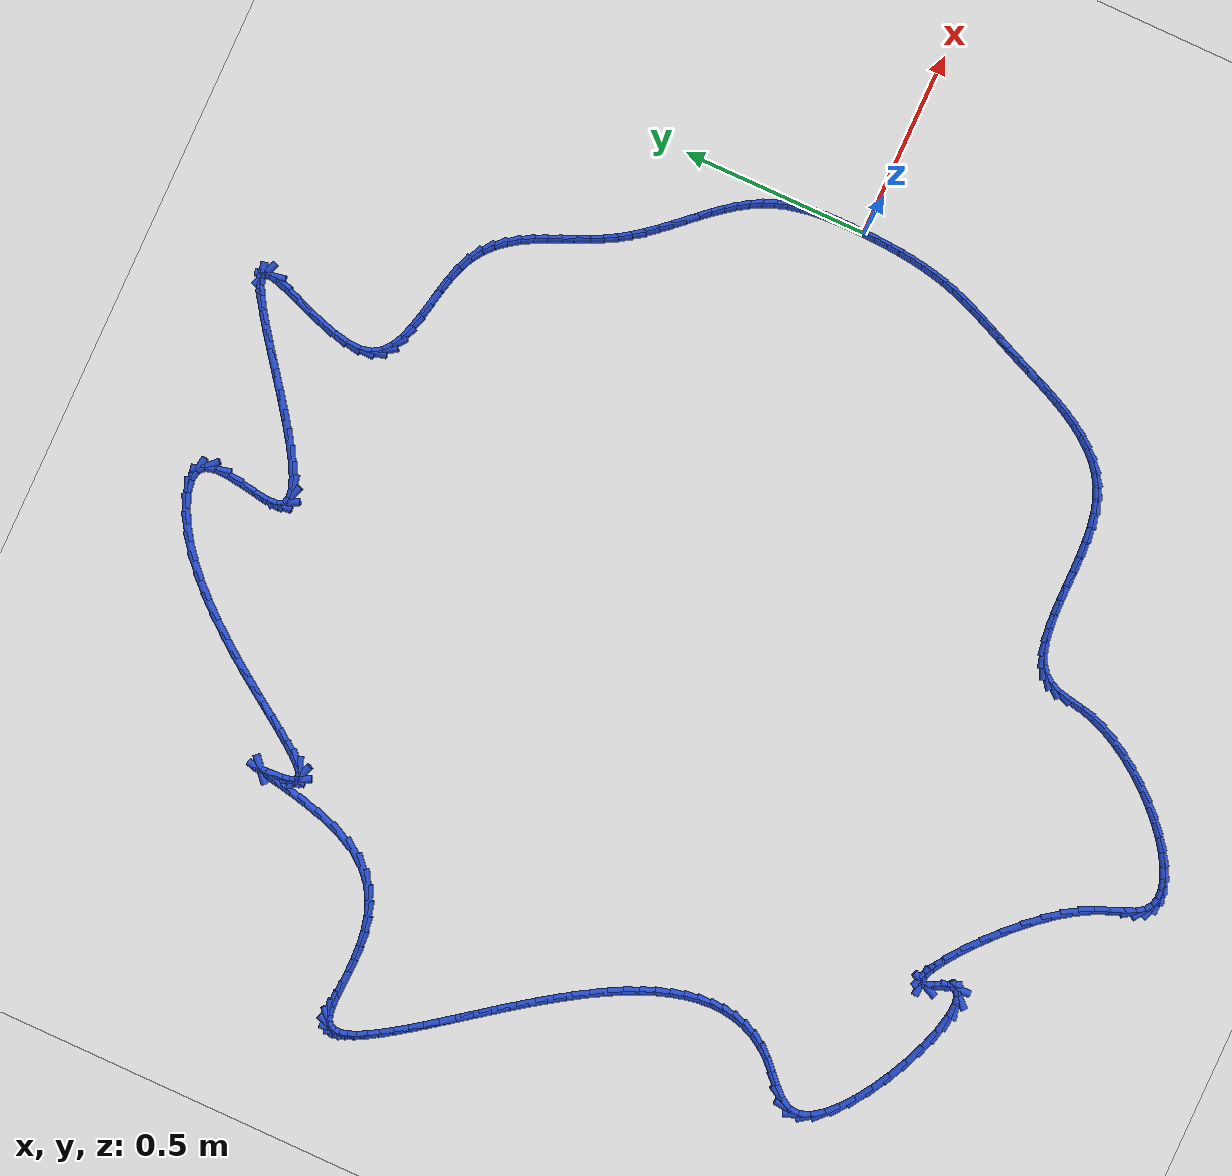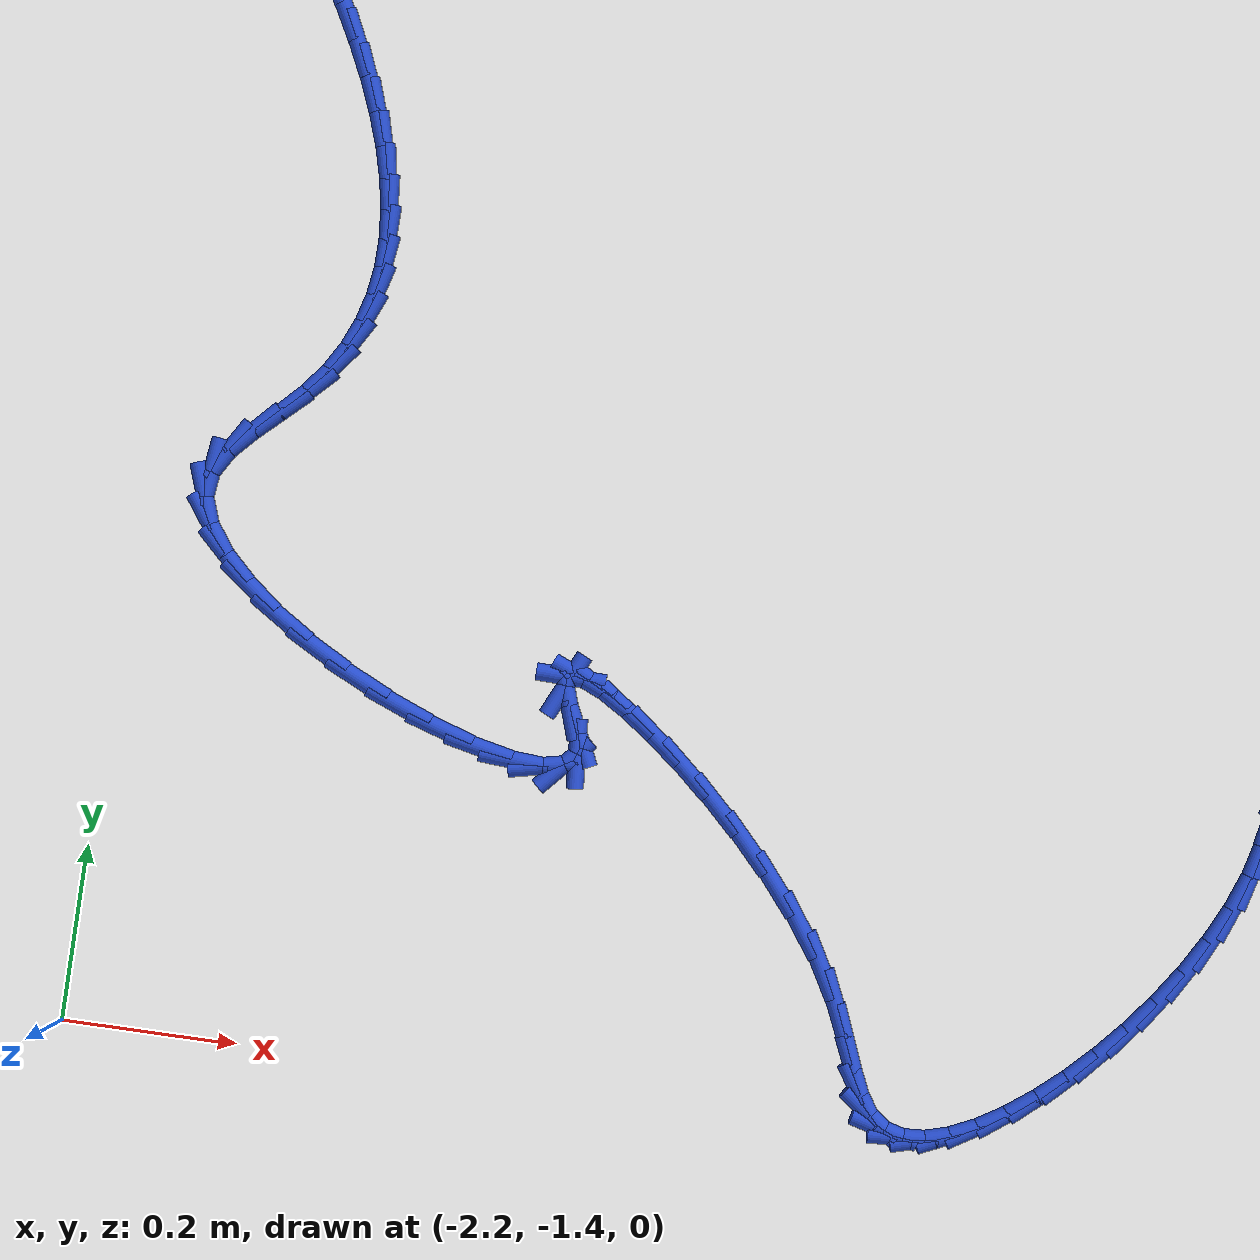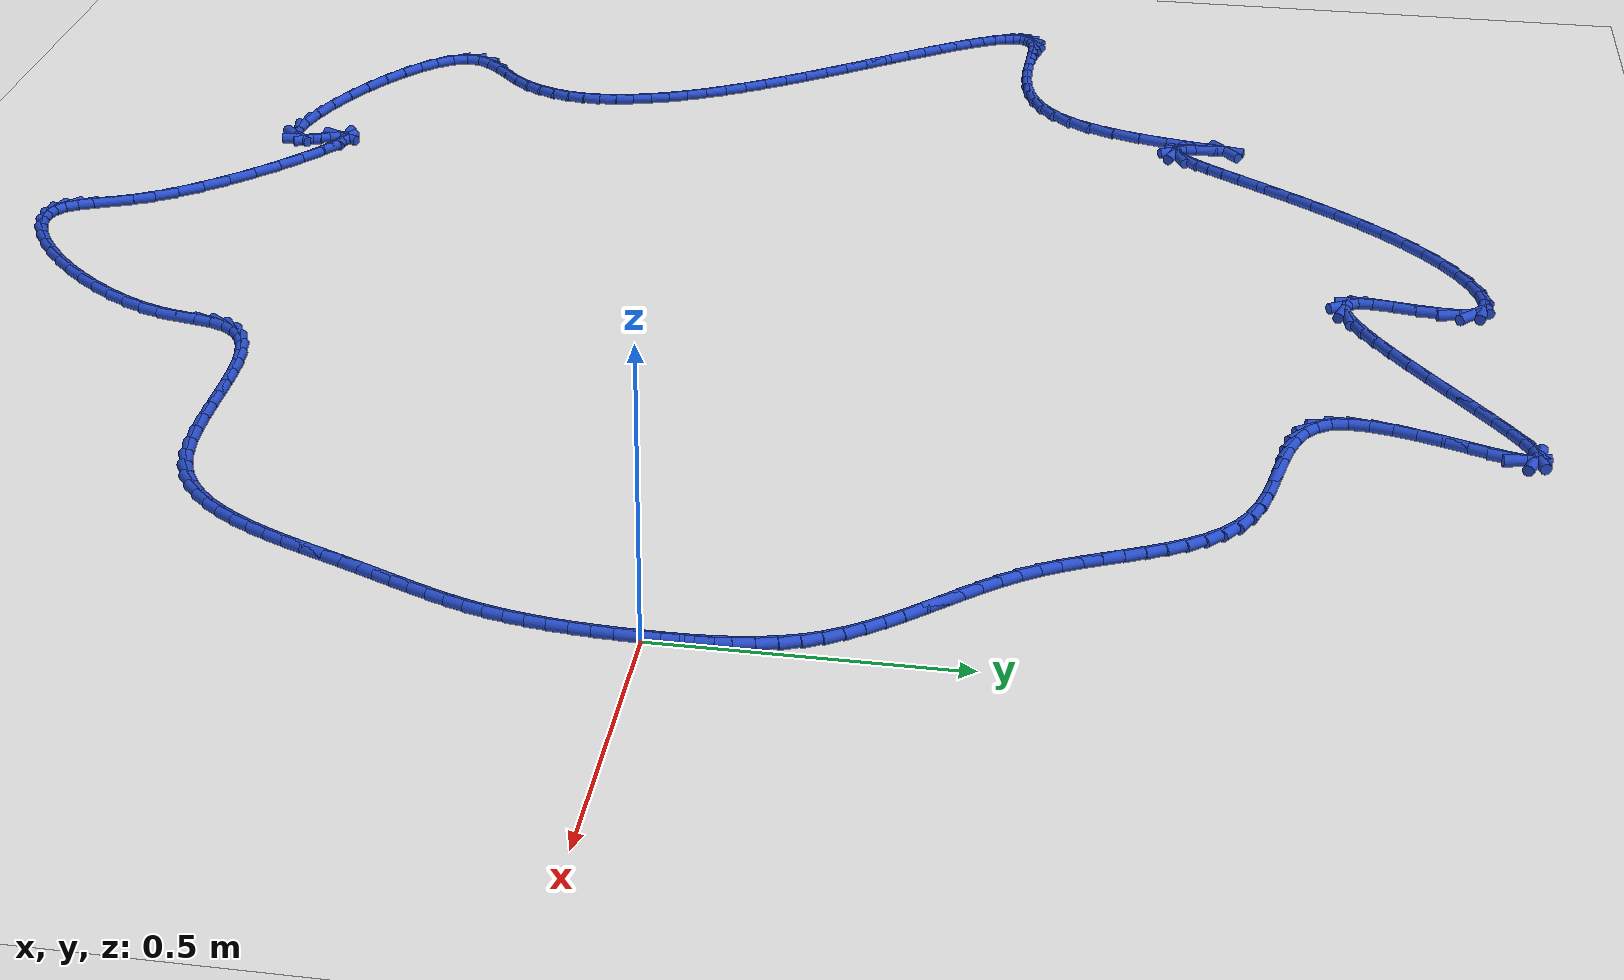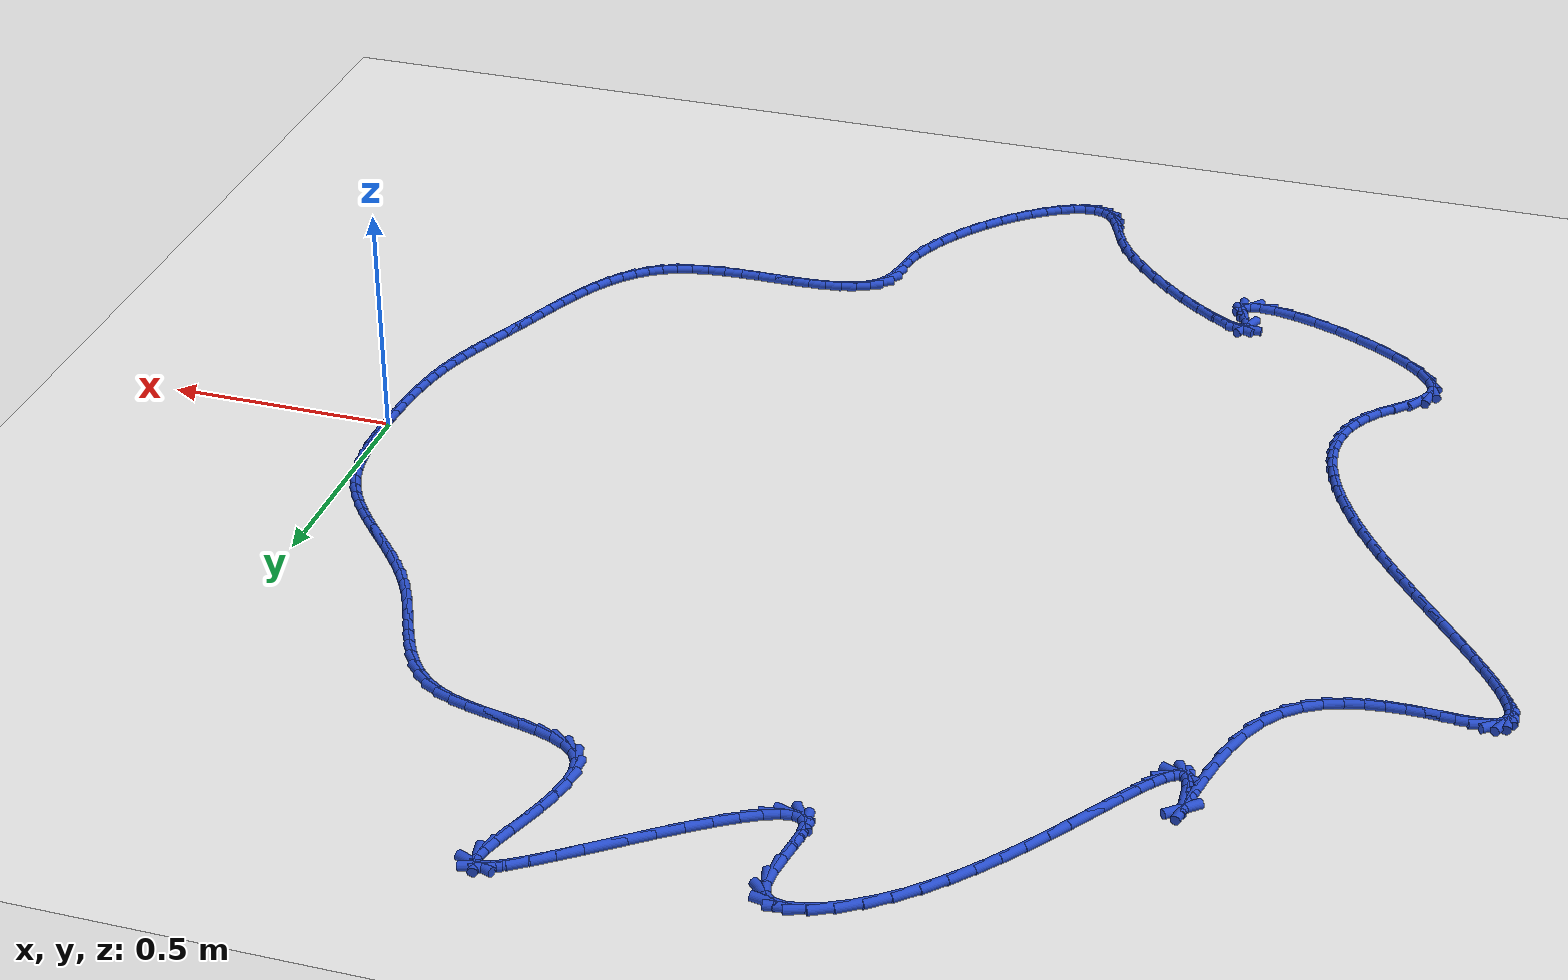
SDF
<sdf version="1.6">
 <world name="default">
  <light name="sun" type="directional">
   <pose>0 0 10 0 -0 0</pose>
   <diffuse>0.8 0.8 0.8 1</diffuse>
   <specular>0.2 0.2 0.2 1</specular>
   <attenuation>
    <range>1000</range>
    <constant>0.9</constant>
    <linear>0.01</linear>
    <quadratic>0.001</quadratic>
   </attenuation>
   <direction>-0.5 0.1 -0.9</direction>
  </light>
  <model name="ground_plane">
   <static>1</static>
   <link name="link">
    <collision name="collision">
     <geometry><plane><normal>0 0 1</normal><size>100 100</size></plane></geometry>
     <surface><friction><ode><mu>100</mu><mu2>50</mu2></ode></friction></surface>
    </collision>
    <visual name="visual">
     <cast_shadows>0</cast_shadows>
     <geometry><plane><normal>0 0 1</normal><size>100 100</size></plane></geometry>
     <material>
      <script><uri>file://media/materials/scripts/gazebo.material</uri><name>Gazebo/WhiteGlow</name></script>
     </material>
    </visual>
   </link>
  </model>
  <gravity>0 0 -9.8</gravity>
  <magnetic_field>6e-06 2.3e-05 -4.2e-05</magnetic_field>
  <atmosphere type="adiabatic"/>
  <physics name="default_physics" default="0" type="ode">
   <max_step_size>0.001</max_step_size>
   <real_time_factor>1</real_time_factor>
   <real_time_update_rate>1000</real_time_update_rate>
  </physics>
  <scene><ambient>0.4 0.4 0.4 1</ambient><background>0.7 0.7 0.7 1</background><shadows>1</shadows></scene>
  <spherical_coordinates>
   <surface_model>EARTH_WGS84</surface_model>
   <latitude_deg>0</latitude_deg>
   <longitude_deg>0</longitude_deg>
   <elevation>0</elevation>
   <heading_deg>0</heading_deg>
  </spherical_coordinates>
  <model name="line">
   <link name="link_0">
    <pose>-2.4936649967166602e-18 1.3877787807814457e-17 0.01 0 1.57 1.55556651719316</pose>
    <collision name="collision">
     <geometry><cylinder><radius>0.01</radius><length>0.08</length></cylinder></geometry>
    </collision>
    <visual name="visual">
     <material>
      <script><name>Gazebo/Blue</name><uri>file://media/materials/scripts/gazebo.material</uri></script>
     </material>
     <geometry><cylinder><radius>0.01</radius><length>0.08</length></cylinder></geometry>
    </visual>
   </link>
   <link name="link_1">
    <pose>0.0005407337437679585 0.035502212440779134 0.01 0 1.57 -1.5596700850896297</pose>
    <collision name="collision">
     <geometry><cylinder><radius>0.01</radius><length>0.08</length></cylinder></geometry>
    </collision>
    <visual name="visual">
     <material>
      <script><name>Gazebo/Blue</name><uri>file://media/materials/scripts/gazebo.material</uri></script>
     </material>
     <geometry><cylinder><radius>0.01</radius><length>0.08</length></cylinder></geometry>
    </visual>
   </link>
   <link name="link_2">
    <pose>0.0001457572536413622 0.07100029004681058 0.01 0 1.57 -1.5233195470723986</pose>
    <collision name="collision">
     <geometry><cylinder><radius>0.01</radius><length>0.08</length></cylinder></geometry>
    </collision>
    <visual name="visual">
     <material>
      <script><name>Gazebo/Blue</name><uri>file://media/materials/scripts/gazebo.material</uri></script>
     </material>
     <geometry><cylinder><radius>0.01</radius><length>0.08</length></cylinder></geometry>
    </visual>
   </link>
   <link name="link_3">
    <pose>-0.0015288611522829391 0.10624615139334401 0.01 0 1.57 -1.4761557841041826</pose>
    <collision name="collision">
     <geometry><cylinder><radius>0.01</radius><length>0.08</length></cylinder></geometry>
    </collision>
    <visual name="visual">
     <material>
      <script><name>Gazebo/Blue</name><uri>file://media/materials/scripts/gazebo.material</uri></script>
     </material>
     <geometry><cylinder><radius>0.01</radius><length>0.08</length></cylinder></geometry>
    </visual>
   </link>
   <link name="link_4">
    <pose>-0.004827053155908098 0.14099171505562902 0.01 0 1.57 -1.417131085236432</pose>
    <collision name="collision">
     <geometry><cylinder><radius>0.01</radius><length>0.08</length></cylinder></geometry>
    </collision>
    <visual name="visual">
     <material>
      <script><name>Gazebo/Blue</name><uri>file://media/materials/scripts/gazebo.material</uri></script>
     </material>
     <geometry><cylinder><radius>0.01</radius><length>0.08</length></cylinder></geometry>
    </visual>
   </link>
   <link name="link_5">
    <pose>-0.010092750439137257 0.17498889960891525 0.01 0 1.57 -1.3451030389582668</pose>
    <collision name="collision">
     <geometry><cylinder><radius>0.01</radius><length>0.08</length></cylinder></geometry>
    </collision>
    <visual name="visual">
     <material>
      <script><name>Gazebo/Blue</name><uri>file://media/materials/scripts/gazebo.material</uri></script>
     </material>
     <geometry><cylinder><radius>0.01</radius><length>0.08</length></cylinder></geometry>
    </visual>
   </link>
   <link name="link_6">
    <pose>-0.017669884683873573 0.20798962362845225 0.01 0 1.57 -1.2590801547431074</pose>
    <collision name="collision">
     <geometry><cylinder><radius>0.01</radius><length>0.08</length></cylinder></geometry>
    </collision>
    <visual name="visual">
     <material>
      <script><name>Gazebo/Blue</name><uri>file://media/materials/scripts/gazebo.material</uri></script>
     </material>
     <geometry><cylinder><radius>0.01</radius><length>0.08</length></cylinder></geometry>
    </visual>
   </link>
   <link name="link_7">
    <pose>-0.027902387572020196 0.2397458056894896 0.01 0 1.57 -1.1602870891569408</pose>
    <collision name="collision">
     <geometry><cylinder><radius>0.01</radius><length>0.08</length></cylinder></geometry>
    </collision>
    <visual name="visual">
     <material>
      <script><name>Gazebo/Blue</name><uri>file://media/materials/scripts/gazebo.material</uri></script>
     </material>
     <geometry><cylinder><radius>0.01</radius><length>0.08</length></cylinder></geometry>
    </visual>
   </link>
   <link name="link_8">
    <pose>-0.04108747601247227 0.2700398645638132 0.01 0 1.57 -1.0662621398742202</pose>
    <collision name="collision">
     <geometry><cylinder><radius>0.01</radius><length>0.08</length></cylinder></geometry>
    </collision>
    <visual name="visual">
     <material>
      <script><name>Gazebo/Blue</name><uri>file://media/materials/scripts/gazebo.material</uri></script>
     </material>
     <geometry><cylinder><radius>0.01</radius><length>0.08</length></cylinder></geometry>
    </visual>
   </link>
   <link name="link_9">
    <pose>-0.057056437079254965 0.2989584258216271 0.01 0 1.57 -0.9882858720722261</pose>
    <collision name="collision">
     <geometry><cylinder><radius>0.01</radius><length>0.08</length></cylinder></geometry>
    </collision>
    <visual name="visual">
     <material>
      <script><name>Gazebo/Blue</name><uri>file://media/materials/scripts/gazebo.material</uri></script>
     </material>
     <geometry><cylinder><radius>0.01</radius><length>0.08</length></cylinder></geometry>
    </visual>
   </link>
   <link name="link_10">
    <pose>-0.07537294183143801 0.3267628422238459 0.01 0 1.57 -0.92707556029061</pose>
    <collision name="collision">
     <geometry><cylinder><radius>0.01</radius><length>0.08</length></cylinder></geometry>
    </collision>
    <visual name="visual">
     <material>
      <script><name>Gazebo/Blue</name><uri>file://media/materials/scripts/gazebo.material</uri></script>
     </material>
     <geometry><cylinder><radius>0.01</radius><length>0.08</length></cylinder></geometry>
    </visual>
   </link>
   <link name="link_11">
    <pose>-0.09559747350886202 0.3537165478668324 0.01 0 1.57 -0.8823351379523636</pose>
    <collision name="collision">
     <geometry><cylinder><radius>0.01</radius><length>0.08</length></cylinder></geometry>
    </collision>
    <visual name="visual">
     <material>
      <script><name>Gazebo/Blue</name><uri>file://media/materials/scripts/gazebo.material</uri></script>
     </material>
     <geometry><cylinder><radius>0.01</radius><length>0.08</length></cylinder></geometry>
    </visual>
   </link>
   <link name="link_12">
    <pose>-0.11729051535136747 0.3800829768469493 0.01 0 1.57 -0.8533866585685161</pose>
    <collision name="collision">
     <geometry><cylinder><radius>0.01</radius><length>0.08</length></cylinder></geometry>
    </collision>
    <visual name="visual">
     <material>
      <script><name>Gazebo/Blue</name><uri>file://media/materials/scripts/gazebo.material</uri></script>
     </material>
     <geometry><cylinder><radius>0.01</radius><length>0.08</length></cylinder></geometry>
    </visual>
   </link>
   <link name="link_13">
    <pose>-0.14001255059879494 0.4061255632605595 0.01 0 1.57 -0.839523905654398</pose>
    <collision name="collision">
     <geometry><cylinder><radius>0.01</radius><length>0.08</length></cylinder></geometry>
    </collision>
    <visual name="visual">
     <material>
      <script><name>Gazebo/Blue</name><uri>file://media/materials/scripts/gazebo.material</uri></script>
     </material>
     <geometry><cylinder><radius>0.01</radius><length>0.08</length></cylinder></geometry>
    </visual>
   </link>
   <link name="link_14">
    <pose>-0.16332406249098497 0.43210774120402573 0.01 0 1.57 -0.8402055397567152</pose>
    <collision name="collision">
     <geometry><cylinder><radius>0.01</radius><length>0.08</length></cylinder></geometry>
    </collision>
    <visual name="visual">
     <material>
      <script><name>Gazebo/Blue</name><uri>file://media/materials/scripts/gazebo.material</uri></script>
     </material>
     <geometry><cylinder><radius>0.01</radius><length>0.08</length></cylinder></geometry>
    </visual>
   </link>
   <link name="link_15">
    <pose>-0.18678553426777803 0.45829294477371063 0.01 0 1.57 -0.8551263353817182</pose>
    <collision name="collision">
     <geometry><cylinder><radius>0.01</radius><length>0.08</length></cylinder></geometry>
    </collision>
    <visual name="visual">
     <material>
      <script><name>Gazebo/Blue</name><uri>file://media/materials/scripts/gazebo.material</uri></script>
     </material>
     <geometry><cylinder><radius>0.01</radius><length>0.08</length></cylinder></geometry>
    </visual>
   </link>
   <link name="link_16">
    <pose>-0.20995744916901488 0.4849446080659775 0.01 0 1.57 -0.8841978674726166</pose>
    <collision name="collision">
     <geometry><cylinder><radius>0.01</radius><length>0.08</length></cylinder></geometry>
    </collision>
    <visual name="visual">
     <material>
      <script><name>Gazebo/Blue</name><uri>file://media/materials/scripts/gazebo.material</uri></script>
     </material>
     <geometry><cylinder><radius>0.01</radius><length>0.08</length></cylinder></geometry>
    </visual>
   </link>
   <link name="link_17">
    <pose>-0.23240029043453575 0.5123261651771882 0.01 0 1.57 -0.9274511577896902</pose>
    <collision name="collision">
     <geometry><cylinder><radius>0.01</radius><length>0.08</length></cylinder></geometry>
    </collision>
    <visual name="visual">
     <material>
      <script><name>Gazebo/Blue</name><uri>file://media/materials/scripts/gazebo.material</uri></script>
     </material>
     <geometry><cylinder><radius>0.01</radius><length>0.08</length></cylinder></geometry>
    </visual>
   </link>
   <link name="link_18">
    <pose>-0.2536745413041813 0.5407010502037062 0.01 0 1.57 -0.9848592951377003</pose>
    <collision name="collision">
     <geometry><cylinder><radius>0.01</radius><length>0.08</length></cylinder></geometry>
    </collision>
    <visual name="visual">
     <material>
      <script><name>Gazebo/Blue</name><uri>file://media/materials/scripts/gazebo.material</uri></script>
     </material>
     <geometry><cylinder><radius>0.01</radius><length>0.08</length></cylinder></geometry>
    </visual>
   </link>
   <link name="link_19">
    <pose>-0.2733406850177922 0.5703326972418941 0.01 0 1.57 -1.0524176009330115</pose>
    <collision name="collision">
     <geometry><cylinder><radius>0.01</radius><length>0.08</length></cylinder></geometry>
    </collision>
    <visual name="visual">
     <material>
      <script><name>Gazebo/Blue</name><uri>file://media/materials/scripts/gazebo.material</uri></script>
     </material>
     <geometry><cylinder><radius>0.01</radius><length>0.08</length></cylinder></geometry>
    </visual>
   </link>
   <link name="link_20">
    <pose>-0.2910648924276981 0.6014053900121284 0.01 0 1.57 -1.1065968287180132</pose>
    <collision name="collision">
     <geometry><cylinder><radius>0.01</radius><length>0.08</length></cylinder></geometry>
    </collision>
    <visual name="visual">
     <material>
      <script><name>Gazebo/Blue</name><uri>file://media/materials/scripts/gazebo.material</uri></script>
     </material>
     <geometry><cylinder><radius>0.01</radius><length>0.08</length></cylinder></geometry>
    </visual>
   </link>
   <link name="link_21">
    <pose>-0.3071847175503509 0.6336006075198406 0.01 0 1.57 -1.1389870851496646</pose>
    <collision name="collision">
     <geometry><cylinder><radius>0.01</radius><length>0.08</length></cylinder></geometry>
    </collision>
    <visual name="visual">
     <material>
      <script><name>Gazebo/Blue</name><uri>file://media/materials/scripts/gazebo.material</uri></script>
     </material>
     <geometry><cylinder><radius>0.01</radius><length>0.08</length></cylinder></geometry>
    </visual>
   </link>
   <link name="link_22">
    <pose>-0.32230048990969673 0.6664030338980236 0.01 0 1.57 -1.1502093565112395</pose>
    <collision name="collision">
     <geometry><cylinder><radius>0.01</radius><length>0.08</length></cylinder></geometry>
    </collision>
    <visual name="visual">
     <material>
      <script><name>Gazebo/Blue</name><uri>file://media/materials/scripts/gazebo.material</uri></script>
     </material>
     <geometry><cylinder><radius>0.01</radius><length>0.08</length></cylinder></geometry>
    </visual>
   </link>
   <link name="link_23">
    <pose>-0.3370131498617055 0.6992968958222338 0.01 0 1.57 -1.1403058005008975</pose>
    <collision name="collision">
     <geometry><cylinder><radius>0.01</radius><length>0.08</length></cylinder></geometry>
    </collision>
    <visual name="visual">
     <material>
      <script><name>Gazebo/Blue</name><uri>file://media/materials/scripts/gazebo.material</uri></script>
     </material>
     <geometry><cylinder><radius>0.01</radius><length>0.08</length></cylinder></geometry>
    </visual>
   </link>
   <link name="link_24">
    <pose>-0.35192363776234725 0.7317664199680269 0.01 0 1.57 -1.1085566555772426</pose>
    <collision name="collision">
     <geometry><cylinder><radius>0.01</radius><length>0.08</length></cylinder></geometry>
    </collision>
    <visual name="visual">
     <material>
      <script><name>Gazebo/Blue</name><uri>file://media/materials/scripts/gazebo.material</uri></script>
     </material>
     <geometry><cylinder><radius>0.01</radius><length>0.08</length></cylinder></geometry>
    </visual>
   </link>
   <link name="link_25">
    <pose>-0.36763289396759186 0.7632958330109593 0.01 0 1.57 -1.0535550653636772</pose>
    <collision name="collision">
     <geometry><cylinder><radius>0.01</radius><length>0.08</length></cylinder></geometry>
    </collision>
    <visual name="visual">
     <material>
      <script><name>Gazebo/Blue</name><uri>file://media/materials/scripts/gazebo.material</uri></script>
     </material>
     <geometry><cylinder><radius>0.01</radius><length>0.08</length></cylinder></geometry>
    </visual>
   </link>
   <link name="link_26">
    <pose>-0.38474185883340933 0.7933693616265868 0.01 0 1.57 -0.9736113542305437</pose>
    <collision name="collision">
     <geometry><cylinder><radius>0.01</radius><length>0.08</length></cylinder></geometry>
    </collision>
    <visual name="visual">
     <material>
      <script><name>Gazebo/Blue</name><uri>file://media/materials/scripts/gazebo.material</uri></script>
     </material>
     <geometry><cylinder><radius>0.01</radius><length>0.08</length></cylinder></geometry>
    </visual>
   </link>
   <link name="link_27">
    <pose>-0.4038514727157696 0.8214712324904654 0.01 0 1.57 -0.8676880570444547</pose>
    <collision name="collision">
     <geometry><cylinder><radius>0.01</radius><length>0.08</length></cylinder></geometry>
    </collision>
    <visual name="visual">
     <material>
      <script><name>Gazebo/Blue</name><uri>file://media/materials/scripts/gazebo.material</uri></script>
     </material>
     <geometry><cylinder><radius>0.01</radius><length>0.08</length></cylinder></geometry>
    </visual>
   </link>
   <link name="link_28">
    <pose>-0.42556267597064257 0.8470856722781511 0.01 0 1.57 -0.7369878495172038</pose>
    <collision name="collision">
     <geometry><cylinder><radius>0.01</radius><length>0.08</length></cylinder></geometry>
    </collision>
    <visual name="visual">
     <material>
      <script><name>Gazebo/Blue</name><uri>file://media/materials/scripts/gazebo.material</uri></script>
     </material>
     <geometry><cylinder><radius>0.01</radius><length>0.08</length></cylinder></geometry>
    </visual>
   </link>
   <link name="link_29">
    <pose>-0.45047640895399843 0.8696969076652002 0.01 0 1.57 -0.5867348057465943</pose>
    <collision name="collision">
     <geometry><cylinder><radius>0.01</radius><length>0.08</length></cylinder></geometry>
    </collision>
    <visual name="visual">
     <material>
      <script><name>Gazebo/Blue</name><uri>file://media/materials/scripts/gazebo.material</uri></script>
     </material>
     <geometry><cylinder><radius>0.01</radius><length>0.08</length></cylinder></geometry>
    </visual>
   </link>
   <link name="link_30">
    <pose>-0.479193612021807 0.8887891653271685 0.01 0 1.57 -0.43130533783535147</pose>
    <collision name="collision">
     <geometry><cylinder><radius>0.01</radius><length>0.08</length></cylinder></geometry>
    </collision>
    <visual name="visual">
     <material>
      <script><name>Gazebo/Blue</name><uri>file://media/materials/scripts/gazebo.material</uri></script>
     </material>
     <geometry><cylinder><radius>0.01</radius><length>0.08</length></cylinder></geometry>
    </visual>
   </link>
   <link name="link_31">
    <pose>-0.5121694494627276 0.9039647072021862 0.01 0 1.57 -0.31400136566931497</pose>
    <collision name="collision">
     <geometry><cylinder><radius>0.01</radius><length>0.08</length></cylinder></geometry>
    </collision>
    <visual name="visual">
     <material>
      <script><name>Gazebo/Blue</name><uri>file://media/materials/scripts/gazebo.material</uri></script>
     </material>
     <geometry><cylinder><radius>0.01</radius><length>0.08</length></cylinder></geometry>
    </visual>
   </link>
   <link name="link_32">
    <pose>-0.5486440115682867 0.9158096438185157 0.01 0 1.57 -0.24343513789368326</pose>
    <collision name="collision">
     <geometry><cylinder><radius>0.01</radius><length>0.08</length></cylinder></geometry>
    </collision>
    <visual name="visual">
     <material>
      <script><name>Gazebo/Blue</name><uri>file://media/materials/scripts/gazebo.material</uri></script>
     </material>
     <geometry><cylinder><radius>0.01</radius><length>0.08</length></cylinder></geometry>
    </visual>
   </link>
   <link name="link_33">
    <pose>-0.5872538166115109 0.9253987995447657 0.01 0 1.57 -0.21045619641111354</pose>
    <collision name="collision">
     <geometry><cylinder><radius>0.01</radius><length>0.08</length></cylinder></geometry>
    </collision>
    <visual name="visual">
     <material>
      <script><name>Gazebo/Blue</name><uri>file://media/materials/scripts/gazebo.material</uri></script>
     </material>
     <geometry><cylinder><radius>0.01</radius><length>0.08</length></cylinder></geometry>
    </visual>
   </link>
   <link name="link_34">
    <pose>-0.6266310168645688 0.9338105339118472 0.01 0 1.57 -0.21117641054036693</pose>
    <collision name="collision">
     <geometry><cylinder><radius>0.01</radius><length>0.08</length></cylinder></geometry>
    </collision>
    <visual name="visual">
     <material>
      <script><name>Gazebo/Blue</name><uri>file://media/materials/scripts/gazebo.material</uri></script>
     </material>
     <geometry><cylinder><radius>0.01</radius><length>0.08</length></cylinder></geometry>
    </visual>
   </link>
   <link name="link_35">
    <pose>-0.6654077645996288 0.9421232064506707 0.01 0 1.57 -0.24727498064319328</pose>
    <collision name="collision">
     <geometry><cylinder><radius>0.01</radius><length>0.08</length></cylinder></geometry>
    </collision>
    <visual name="visual">
     <material>
      <script><name>Gazebo/Blue</name><uri>file://media/materials/scripts/gazebo.material</uri></script>
     </material>
     <geometry><cylinder><radius>0.01</radius><length>0.08</length></cylinder></geometry>
    </visual>
   </link>
   <link name="link_36">
    <pose>-0.70221621208886 0.9514151766921469 0.01 0 1.57 -0.3269093243362142</pose>
    <collision name="collision">
     <geometry><cylinder><radius>0.01</radius><length>0.08</length></cylinder></geometry>
    </collision>
    <visual name="visual">
     <material>
      <script><name>Gazebo/Blue</name><uri>file://media/materials/scripts/gazebo.material</uri></script>
     </material>
     <geometry><cylinder><radius>0.01</radius><length>0.08</length></cylinder></geometry>
    </visual>
   </link>
   <link name="link_37">
    <pose>-0.7356885116044303 0.9627648041671869 0.01 0 1.57 -0.4664659619714852</pose>
    <collision name="collision">
     <geometry><cylinder><radius>0.01</radius><length>0.08</length></cylinder></geometry>
    </collision>
    <visual name="visual">
     <material>
      <script><name>Gazebo/Blue</name><uri>file://media/materials/scripts/gazebo.material</uri></script>
     </material>
     <geometry><cylinder><radius>0.01</radius><length>0.08</length></cylinder></geometry>
    </visual>
   </link>
   <link name="link_38">
    <pose>-0.7644568154185091 0.9772504484067013 0.01 0 1.57 -0.6891558496404054</pose>
    <collision name="collision">
     <geometry><cylinder><radius>0.01</radius><length>0.08</length></cylinder></geometry>
    </collision>
    <visual name="visual">
     <material>
      <script><name>Gazebo/Blue</name><uri>file://media/materials/scripts/gazebo.material</uri></script>
     </material>
     <geometry><cylinder><radius>0.01</radius><length>0.08</length></cylinder></geometry>
    </visual>
   </link>
   <link name="link_39">
    <pose>-0.7871532758032648 0.9959504689416007 0.01 0 1.57 -1.0044038426361575</pose>
    <collision name="collision">
     <geometry><cylinder><radius>0.01</radius><length>0.08</length></cylinder></geometry>
    </collision>
    <visual name="visual">
     <material>
      <script><name>Gazebo/Blue</name><uri>file://media/materials/scripts/gazebo.material</uri></script>
     </material>
     <geometry><cylinder><radius>0.01</radius><length>0.08</length></cylinder></geometry>
    </visual>
   </link>
   <link name="link_40">
    <pose>-0.802410045030866 1.0199432253027962 0.01 0 1.57 -1.355166654693067</pose>
    <collision name="collision">
     <geometry><cylinder><radius>0.01</radius><length>0.08</length></cylinder></geometry>
    </collision>
    <visual name="visual">
     <material>
      <script><name>Gazebo/Blue</name><uri>file://media/materials/scripts/gazebo.material</uri></script>
     </material>
     <geometry><cylinder><radius>0.01</radius><length>0.08</length></cylinder></geometry>
    </visual>
   </link>
   <link name="link_41">
    <pose>-0.8090279150845493 1.0501569808338767 0.01 0 1.57 1.533358573759522</pose>
    <collision name="collision">
     <geometry><cylinder><radius>0.01</radius><length>0.08</length></cylinder></geometry>
    </collision>
    <visual name="visual">
     <material>
      <script><name>Gazebo/Blue</name><uri>file://media/materials/scripts/gazebo.material</uri></script>
     </material>
     <geometry><cylinder><radius>0.01</radius><length>0.08</length></cylinder></geometry>
    </visual>
   </link>
   <link name="link_42">
    <pose>-0.8076912663839207 1.0858435287220813 0.01 0 1.57 1.384298192352535</pose>
    <collision name="collision">
     <geometry><cylinder><radius>0.01</radius><length>0.08</length></cylinder></geometry>
    </collision>
    <visual name="visual">
     <material>
      <script><name>Gazebo/Blue</name><uri>file://media/materials/scripts/gazebo.material</uri></script>
     </material>
     <geometry><cylinder><radius>0.01</radius><length>0.08</length></cylinder></geometry>
    </visual>
   </link>
   <link name="link_43">
    <pose>-0.8002641752650999 1.125204684909398 0.01 0 1.57 1.2956894341613683</pose>
    <collision name="collision">
     <geometry><cylinder><radius>0.01</radius><length>0.08</length></cylinder></geometry>
    </collision>
    <visual name="visual">
     <material>
      <script><name>Gazebo/Blue</name><uri>file://media/materials/scripts/gazebo.material</uri></script>
     </material>
     <geometry><cylinder><radius>0.01</radius><length>0.08</length></cylinder></geometry>
    </visual>
   </link>
   <link name="link_44">
    <pose>-0.7886288436129738 1.1664261328637602 0.01 0 1.57 1.2445693837532175</pose>
    <collision name="collision">
     <geometry><cylinder><radius>0.01</radius><length>0.08</length></cylinder></geometry>
    </collision>
    <visual name="visual">
     <material>
      <script><name>Gazebo/Blue</name><uri>file://media/materials/scripts/gazebo.material</uri></script>
     </material>
     <geometry><cylinder><radius>0.01</radius><length>0.08</length></cylinder></geometry>
    </visual>
   </link>
   <link name="link_45">
    <pose>-0.7746674733124307 1.2076935560531032 0.01 0 1.57 1.2210886437733606</pose>
    <collision name="collision">
     <geometry><cylinder><radius>0.01</radius><length>0.08</length></cylinder></geometry>
    </collision>
    <visual name="visual">
     <material>
      <script><name>Gazebo/Blue</name><uri>file://media/materials/scripts/gazebo.material</uri></script>
     </material>
     <geometry><cylinder><radius>0.01</radius><length>0.08</length></cylinder></geometry>
    </visual>
   </link>
   <link name="link_46">
    <pose>-0.7602622662483584 1.2471926379453608 0.01 0 1.57 1.2243308106100692</pose>
    <collision name="collision">
     <geometry><cylinder><radius>0.01</radius><length>0.08</length></cylinder></geometry>
    </collision>
    <visual name="visual">
     <material>
      <script><name>Gazebo/Blue</name><uri>file://media/materials/scripts/gazebo.material</uri></script>
     </material>
     <geometry><cylinder><radius>0.01</radius><length>0.08</length></cylinder></geometry>
    </visual>
   </link>
   <link name="link_47">
    <pose>-0.7472954243056444 1.2831090620084673 0.01 0 1.57 1.2646626121236766</pose>
    <collision name="collision">
     <geometry><cylinder><radius>0.01</radius><length>0.08</length></cylinder></geometry>
    </collision>
    <visual name="visual">
     <material>
      <script><name>Gazebo/Blue</name><uri>file://media/materials/scripts/gazebo.material</uri></script>
     </material>
     <geometry><cylinder><radius>0.01</radius><length>0.08</length></cylinder></geometry>
    </visual>
   </link>
   <link name="link_48">
    <pose>-0.737649149369177 1.313628511710357 0.01 0 1.57 1.382415151785069</pose>
    <collision name="collision">
     <geometry><cylinder><radius>0.01</radius><length>0.08</length></cylinder></geometry>
    </collision>
    <visual name="visual">
     <material>
      <script><name>Gazebo/Blue</name><uri>file://media/materials/scripts/gazebo.material</uri></script>
     </material>
     <geometry><cylinder><radius>0.01</radius><length>0.08</length></cylinder></geometry>
    </visual>
   </link>
   <link name="link_49">
    <pose>-0.7332056433238435 1.3369366705189636 0.01 0 1.57 -1.3879835540624126</pose>
    <collision name="collision">
     <geometry><cylinder><radius>0.01</radius><length>0.08</length></cylinder></geometry>
    </collision>
    <visual name="visual">
     <material>
      <script><name>Gazebo/Blue</name><uri>file://media/materials/scripts/gazebo.material</uri></script>
     </material>
     <geometry><cylinder><radius>0.01</radius><length>0.08</length></cylinder></geometry>
    </visual>
   </link>
   <link name="link_50">
    <pose>-0.7358463157382616 1.351220076887639 0.01 0 1.57 -0.3645471963744435</pose>
    <collision name="collision">
     <geometry><cylinder><radius>0.01</radius><length>0.08</length></cylinder></geometry>
    </collision>
    <visual name="visual">
     <material>
      <script><name>Gazebo/Blue</name><uri>file://media/materials/scripts/gazebo.material</uri></script>
     </material>
     <geometry><cylinder><radius>0.01</radius><length>0.08</length></cylinder></geometry>
    </visual>
   </link>
   <link name="link_51">
    <pose>-0.7467790672484634 1.3553920501485872 0.01 0 1.57 0.2623074517618695</pose>
    <collision name="collision">
     <geometry><cylinder><radius>0.01</radius><length>0.08</length></cylinder></geometry>
    </collision>
    <visual name="visual">
     <material>
      <script><name>Gazebo/Blue</name><uri>file://media/materials/scripts/gazebo.material</uri></script>
     </material>
     <geometry><cylinder><radius>0.01</radius><length>0.08</length></cylinder></geometry>
    </visual>
   </link>
   <link name="link_52">
    <pose>-0.765311879546534 1.3504161048029624 0.01 0 1.57 0.47149615954381424</pose>
    <collision name="collision">
     <geometry><cylinder><radius>0.01</radius><length>0.08</length></cylinder></geometry>
    </collision>
    <visual name="visual">
     <material>
      <script><name>Gazebo/Blue</name><uri>file://media/materials/scripts/gazebo.material</uri></script>
     </material>
     <geometry><cylinder><radius>0.01</radius><length>0.08</length></cylinder></geometry>
    </visual>
   </link>
   <link name="link_53">
    <pose>-0.7904201169989908 1.3376146814188272 0.01 0 1.57 0.5619362551408126</pose>
    <collision name="collision">
     <geometry><cylinder><radius>0.01</radius><length>0.08</length></cylinder></geometry>
    </collision>
    <visual name="visual">
     <material>
      <script><name>Gazebo/Blue</name><uri>file://media/materials/scripts/gazebo.material</uri></script>
     </material>
     <geometry><cylinder><radius>0.01</radius><length>0.08</length></cylinder></geometry>
    </visual>
   </link>
   <link name="link_54">
    <pose>-0.8210791439723515 1.3183102205642412 0.01 0 1.57 0.6079630547331005</pose>
    <collision name="collision">
     <geometry><cylinder><radius>0.01</radius><length>0.08</length></cylinder></geometry>
    </collision>
    <visual name="visual">
     <material>
      <script><name>Gazebo/Blue</name><uri>file://media/materials/scripts/gazebo.material</uri></script>
     </material>
     <geometry><cylinder><radius>0.01</radius><length>0.08</length></cylinder></geometry>
    </visual>
   </link>
   <link name="link_55">
    <pose>-0.8562643248331331 1.293825162807265 0.01 0 1.57 0.6322943009306978</pose>
    <collision name="collision">
     <geometry><cylinder><radius>0.01</radius><length>0.08</length></cylinder></geometry>
    </collision>
    <visual name="visual">
     <material>
      <script><name>Gazebo/Blue</name><uri>file://media/materials/scripts/gazebo.material</uri></script>
     </material>
     <geometry><cylinder><radius>0.01</radius><length>0.08</length></cylinder></geometry>
    </visual>
   </link>
   <link name="link_56">
    <pose>-0.8949510239478529 1.2654819487159596 0.01 0 1.57 0.6435981748133929</pose>
    <collision name="collision">
     <geometry><cylinder><radius>0.01</radius><length>0.08</length></cylinder></geometry>
    </collision>
    <visual name="visual">
     <material>
      <script><name>Gazebo/Blue</name><uri>file://media/materials/scripts/gazebo.material</uri></script>
     </material>
     <geometry><cylinder><radius>0.01</radius><length>0.08</length></cylinder></geometry>
    </visual>
   </link>
   <link name="link_57">
    <pose>-0.9361146056830284 1.234603018858386 0.01 0 1.57 0.6454555720517582</pose>
    <collision name="collision">
     <geometry><cylinder><radius>0.01</radius><length>0.08</length></cylinder></geometry>
    </collision>
    <visual name="visual">
     <material>
      <script><name>Gazebo/Blue</name><uri>file://media/materials/scripts/gazebo.material</uri></script>
     </material>
     <geometry><cylinder><radius>0.01</radius><length>0.08</length></cylinder></geometry>
    </visual>
   </link>
   <link name="link_58">
    <pose>-0.9787304344051765 1.2025108138026046 0.01 0 1.57 0.6390324356585301</pose>
    <collision name="collision">
     <geometry><cylinder><radius>0.01</radius><length>0.08</length></cylinder></geometry>
    </collision>
    <visual name="visual">
     <material>
      <script><name>Gazebo/Blue</name><uri>file://media/materials/scripts/gazebo.material</uri></script>
     </material>
     <geometry><cylinder><radius>0.01</radius><length>0.08</length></cylinder></geometry>
    </visual>
   </link>
   <link name="link_59">
    <pose>-1.0217738744808147 1.1705277741166757 0.01 0 1.57 0.6238681012312358</pose>
    <collision name="collision">
     <geometry><cylinder><radius>0.01</radius><length>0.08</length></cylinder></geometry>
    </collision>
    <visual name="visual">
     <material>
      <script><name>Gazebo/Blue</name><uri>file://media/materials/scripts/gazebo.material</uri></script>
     </material>
     <geometry><cylinder><radius>0.01</radius><length>0.08</length></cylinder></geometry>
    </visual>
   </link>
   <link name="link_60">
    <pose>-1.06422029027646 1.1399763403686607 0.01 0 1.57 0.5977886635563228</pose>
    <collision name="collision">
     <geometry><cylinder><radius>0.01</radius><length>0.08</length></cylinder></geometry>
    </collision>
    <visual name="visual">
     <material>
      <script><name>Gazebo/Blue</name><uri>file://media/materials/scripts/gazebo.material</uri></script>
     </material>
     <geometry><cylinder><radius>0.01</radius><length>0.08</length></cylinder></geometry>
    </visual>
   </link>
   <link name="link_61">
    <pose>-1.10504504615863 1.1121789531266197 0.01 0 1.57 0.555945984451621</pose>
    <collision name="collision">
     <geometry><cylinder><radius>0.01</radius><length>0.08</length></cylinder></geometry>
    </collision>
    <visual name="visual">
     <material>
      <script><name>Gazebo/Blue</name><uri>file://media/materials/scripts/gazebo.material</uri></script>
     </material>
     <geometry><cylinder><radius>0.01</radius><length>0.08</length></cylinder></geometry>
    </visual>
   </link>
   <link name="link_62">
    <pose>-1.1432235064938423 1.0884580529586139 0.01 0 1.57 0.4881044734293043</pose>
    <collision name="collision">
     <geometry><cylinder><radius>0.01</radius><length>0.08</length></cylinder></geometry>
    </collision>
    <visual name="visual">
     <material>
      <script><name>Gazebo/Blue</name><uri>file://media/materials/scripts/gazebo.material</uri></script>
     </material>
     <geometry><cylinder><radius>0.01</radius><length>0.08</length></cylinder></geometry>
    </visual>
   </link>
   <link name="link_63">
    <pose>-1.177731035648614 1.0701360804327036 0.01 0 1.57 0.37109707915284335</pose>
    <collision name="collision">
     <geometry><cylinder><radius>0.01</radius><length>0.08</length></cylinder></geometry>
    </collision>
    <visual name="visual">
     <material>
      <script><name>Gazebo/Blue</name><uri>file://media/materials/scripts/gazebo.material</uri></script>
     </material>
     <geometry><cylinder><radius>0.01</radius><length>0.08</length></cylinder></geometry>
    </visual>
   </link>
   <link name="link_64">
    <pose>-1.2075429979894614 1.0585354761169494 0.01 0 1.57 0.14657653851748517</pose>
    <collision name="collision">
     <geometry><cylinder><radius>0.01</radius><length>0.08</length></cylinder></geometry>
    </collision>
    <visual name="visual">
     <material>
      <script><name>Gazebo/Blue</name><uri>file://media/materials/scripts/gazebo.material</uri></script>
     </material>
     <geometry><cylinder><radius>0.01</radius><length>0.08</length></cylinder></geometry>
    </visual>
   </link>
   <link name="link_65">
    <pose>-1.2316347578829032 1.0549786805794126 0.01 0 1.57 -0.3231583201913348</pose>
    <collision name="collision">
     <geometry><cylinder><radius>0.01</radius><length>0.08</length></cylinder></geometry>
    </collision>
    <visual name="visual">
     <material>
      <script><name>Gazebo/Blue</name><uri>file://media/materials/scripts/gazebo.material</uri></script>
     </material>
     <geometry><cylinder><radius>0.01</radius><length>0.08</length></cylinder></geometry>
    </visual>
   </link>
   <link name="link_66">
    <pose>-1.2489816796954558 1.0607881343881533 0.01 0 1.57 -1.0448259775013014</pose>
    <collision name="collision">
     <geometry><cylinder><radius>0.01</radius><length>0.08</length></cylinder></geometry>
    </collision>
    <visual name="visual">
     <material>
      <script><name>Gazebo/Blue</name><uri>file://media/materials/scripts/gazebo.material</uri></script>
     </material>
     <geometry><cylinder><radius>0.01</radius><length>0.08</length></cylinder></geometry>
    </visual>
   </link>
   <link name="link_67">
    <pose>-1.258559127793637 1.0772862781112325 0.01 0 1.57 -1.5194724999171398</pose>
    <collision name="collision">
     <geometry><cylinder><radius>0.01</radius><length>0.08</length></cylinder></geometry>
    </collision>
    <visual name="visual">
     <material>
      <script><name>Gazebo/Blue</name><uri>file://media/materials/scripts/gazebo.material</uri></script>
     </material>
     <geometry><cylinder><radius>0.01</radius><length>0.08</length></cylinder></geometry>
    </visual>
   </link>
   <link name="link_68">
    <pose>-1.2599828690397379 1.1050022728854256 0.01 0 1.57 1.453924606464601</pose>
    <collision name="collision">
     <geometry><cylinder><radius>0.01</radius><length>0.08</length></cylinder></geometry>
    </collision>
    <visual name="visual">
     <material>
      <script><name>Gazebo/Blue</name><uri>file://media/materials/scripts/gazebo.material</uri></script>
     </material>
     <geometry><cylinder><radius>0.01</radius><length>0.08</length></cylinder></geometry>
    </visual>
   </link>
   <link name="link_69">
    <pose>-1.25577186941147 1.1408690288047874 0.01 0 1.57 1.4093247199140935</pose>
    <collision name="collision">
     <geometry><cylinder><radius>0.01</radius><length>0.08</length></cylinder></geometry>
    </collision>
    <visual name="visual">
     <material>
      <script><name>Gazebo/Blue</name><uri>file://media/materials/scripts/gazebo.material</uri></script>
     </material>
     <geometry><cylinder><radius>0.01</radius><length>0.08</length></cylinder></geometry>
    </visual>
   </link>
   <link name="link_70">
    <pose>-1.2492673810902013 1.1808008735307702 0.01 0 1.57 1.4349184412844749</pose>
    <collision name="collision">
     <geometry><cylinder><radius>0.01</radius><length>0.08</length></cylinder></geometry>
    </collision>
    <visual name="visual">
     <material>
      <script><name>Gazebo/Blue</name><uri>file://media/materials/scripts/gazebo.material</uri></script>
     </material>
     <geometry><cylinder><radius>0.01</radius><length>0.08</length></cylinder></geometry>
    </visual>
   </link>
   <link name="link_71">
    <pose>-1.2438107089595731 1.2207120694414633 0.01 0 1.57 1.5409893010086426</pose>
    <collision name="collision">
     <geometry><cylinder><radius>0.01</radius><length>0.08</length></cylinder></geometry>
    </collision>
    <visual name="visual">
     <material>
      <script><name>Gazebo/Blue</name><uri>file://media/materials/scripts/gazebo.material</uri></script>
     </material>
     <geometry><cylinder><radius>0.01</radius><length>0.08</length></cylinder></geometry>
    </visual>
   </link>
   <link name="link_72">
    <pose>-1.242743157903225 1.2565168789149554 0.01 0 1.57 -1.3340247727599028</pose>
    <collision name="collision">
     <geometry><cylinder><radius>0.01</radius><length>0.08</length></cylinder></geometry>
    </collision>
    <visual name="visual">
     <material>
      <script><name>Gazebo/Blue</name><uri>file://media/materials/scripts/gazebo.material</uri></script>
     </material>
     <geometry><cylinder><radius>0.01</radius><length>0.08</length></cylinder></geometry>
    </visual>
   </link>
   <link name="link_73">
    <pose>-1.2494060328047978 1.2841295643293358 0.01 0 1.57 -0.7539144972013343</pose>
    <collision name="collision">
     <geometry><cylinder><radius>0.01</radius><length>0.08</length></cylinder></geometry>
    </collision>
    <visual name="visual">
     <material>
      <script><name>Gazebo/Blue</name><uri>file://media/materials/scripts/gazebo.material</uri></script>
     </material>
     <geometry><cylinder><radius>0.01</radius><length>0.08</length></cylinder></geometry>
    </visual>
   </link>
   <link name="link_74">
    <pose>-1.266452386490176 1.3001349830888704 0.01 0 1.57 -0.16989779764663188</pose>
    <collision name="collision">
     <geometry><cylinder><radius>0.01</radius><length>0.08</length></cylinder></geometry>
    </collision>
    <visual name="visual">
     <material>
      <script><name>Gazebo/Blue</name><uri>file://media/materials/scripts/gazebo.material</uri></script>
     </material>
     <geometry><cylinder><radius>0.01</radius><length>0.08</length></cylinder></geometry>
    </visual>
   </link>
   <link name="link_75">
    <pose>-1.2928894302079432 1.304670300506552 0.01 0 1.57 0.16573971584571326</pose>
    <collision name="collision">
     <geometry><cylinder><radius>0.01</radius><length>0.08</length></cylinder></geometry>
    </collision>
    <visual name="visual">
     <material>
      <script><name>Gazebo/Blue</name><uri>file://media/materials/scripts/gazebo.material</uri></script>
     </material>
     <geometry><cylinder><radius>0.01</radius><length>0.08</length></cylinder></geometry>
    </visual>
   </link>
   <link name="link_76">
    <pose>-1.3265217155345135 1.299044487464639 0.01 0 1.57 0.3585549631792689</pose>
    <collision name="collision">
     <geometry><cylinder><radius>0.01</radius><length>0.08</length></cylinder></geometry>
    </collision>
    <visual name="visual">
     <material>
      <script><name>Gazebo/Blue</name><uri>file://media/materials/scripts/gazebo.material</uri></script>
     </material>
     <geometry><cylinder><radius>0.01</radius><length>0.08</length></cylinder></geometry>
    </visual>
   </link>
   <link name="link_77">
    <pose>-1.3651530477376101 1.2845672420076182 0.01 0 1.57 0.4884670050356795</pose>
    <collision name="collision">
     <geometry><cylinder><radius>0.01</radius><length>0.08</length></cylinder></geometry>
    </collision>
    <visual name="visual">
     <material>
      <script><name>Gazebo/Blue</name><uri>file://media/materials/scripts/gazebo.material</uri></script>
     </material>
     <geometry><cylinder><radius>0.01</radius><length>0.08</length></cylinder></geometry>
    </visual>
   </link>
   <link name="link_78">
    <pose>-1.4065872320849544 1.262548262179974 0.01 0 1.57 0.5916736825576479</pose>
    <collision name="collision">
     <geometry><cylinder><radius>0.01</radius><length>0.08</length></cylinder></geometry>
    </collision>
    <visual name="visual">
     <material>
      <script><name>Gazebo/Blue</name><uri>file://media/materials/scripts/gazebo.material</uri></script>
     </material>
     <geometry><cylinder><radius>0.01</radius><length>0.08</length></cylinder></geometry>
    </visual>
   </link>
   <link name="link_79">
    <pose>-1.4486287073273438 1.2342971320164955 0.01 0 1.57 0.6822285112587788</pose>
    <collision name="collision">
     <geometry><cylinder><radius>0.01</radius><length>0.08</length></cylinder></geometry>
    </collision>
    <visual name="visual">
     <material>
      <script><name>Gazebo/Blue</name><uri>file://media/materials/scripts/gazebo.material</uri></script>
     </material>
     <geometry><cylinder><radius>0.01</radius><length>0.08</length></cylinder></geometry>
    </visual>
   </link>
   <link name="link_80">
    <pose>-1.4895743051197081 1.2010348182428865 0.01 0 1.57 0.7565078281490967</pose>
    <collision name="collision">
     <geometry><cylinder><radius>0.01</radius><length>0.08</length></cylinder></geometry>
    </collision>
    <visual name="visual">
     <material>
      <script><name>Gazebo/Blue</name><uri>file://media/materials/scripts/gazebo.material</uri></script>
     </material>
     <geometry><cylinder><radius>0.01</radius><length>0.08</length></cylinder></geometry>
    </visual>
   </link>
   <link name="link_81">
    <pose>-1.5290938964789877 1.1637351779037266 0.01 0 1.57 0.816061124799054</pose>
    <collision name="collision">
     <geometry><cylinder><radius>0.01</radius><length>0.08</length></cylinder></geometry>
    </collision>
    <visual name="visual">
     <material>
      <script><name>Gazebo/Blue</name><uri>file://media/materials/scripts/gazebo.material</uri></script>
     </material>
     <geometry><cylinder><radius>0.01</radius><length>0.08</length></cylinder></geometry>
    </visual>
   </link>
   <link name="link_82">
    <pose>-1.5670948041985655 1.1233293331924448 0.01 0 1.57 0.863639317143502</pose>
    <collision name="collision">
     <geometry><cylinder><radius>0.01</radius><length>0.08</length></cylinder></geometry>
    </collision>
    <visual name="visual">
     <material>
      <script><name>Gazebo/Blue</name><uri>file://media/materials/scripts/gazebo.material</uri></script>
     </material>
     <geometry><cylinder><radius>0.01</radius><length>0.08</length></cylinder></geometry>
    </visual>
   </link>
   <link name="link_83">
    <pose>-1.6034843510718224 1.080748406302469 0.01 0 1.57 0.9012863477476284</pose>
    <collision name="collision">
     <geometry><cylinder><radius>0.01</radius><length>0.08</length></cylinder></geometry>
    </collision>
    <visual name="visual">
     <material>
      <script><name>Gazebo/Blue</name><uri>file://media/materials/scripts/gazebo.material</uri></script>
     </material>
     <geometry><cylinder><radius>0.01</radius><length>0.08</length></cylinder></geometry>
    </visual>
   </link>
   <link name="link_84">
    <pose>-1.638169859892142 1.0369235194272286 0.01 0 1.57 0.9304127438363866</pose>
    <collision name="collision">
     <geometry><cylinder><radius>0.01</radius><length>0.08</length></cylinder></geometry>
    </collision>
    <visual name="visual">
     <material>
      <script><name>Gazebo/Blue</name><uri>file://media/materials/scripts/gazebo.material</uri></script>
     </material>
     <geometry><cylinder><radius>0.01</radius><length>0.08</length></cylinder></geometry>
    </visual>
   </link>
   <link name="link_85">
    <pose>-1.671058653452905 0.9927857947601519 0.01 0 1.57 0.9518552612427992</pose>
    <collision name="collision">
     <geometry><cylinder><radius>0.01</radius><length>0.08</length></cylinder></geometry>
    </collision>
    <visual name="visual">
     <material>
      <script><name>Gazebo/Blue</name><uri>file://media/materials/scripts/gazebo.material</uri></script>
     </material>
     <geometry><cylinder><radius>0.01</radius><length>0.08</length></cylinder></geometry>
    </visual>
   </link>
   <link name="link_86">
    <pose>-1.702058054547495 0.9492663544946681 0.01 0 1.57 0.9658776120048262</pose>
    <collision name="collision">
     <geometry><cylinder><radius>0.01</radius><length>0.08</length></cylinder></geometry>
    </collision>
    <visual name="visual">
     <material>
      <script><name>Gazebo/Blue</name><uri>file://media/materials/scripts/gazebo.material</uri></script>
     </material>
     <geometry><cylinder><radius>0.01</radius><length>0.08</length></cylinder></geometry>
    </visual>
   </link>
   <link name="link_87">
    <pose>-1.731075385969294 0.9072963208242057 0.01 0 1.57 0.9720676805861276</pose>
    <collision name="collision">
     <geometry><cylinder><radius>0.01</radius><length>0.08</length></cylinder></geometry>
    </collision>
    <visual name="visual">
     <material>
      <script><name>Gazebo/Blue</name><uri>file://media/materials/scripts/gazebo.material</uri></script>
     </material>
     <geometry><cylinder><radius>0.01</radius><length>0.08</length></cylinder></geometry>
    </visual>
   </link>
   <link name="link_88">
    <pose>-1.7580179705116834 0.8678068159421941 0.01 0 1.57 0.9690430360633145</pose>
    <collision name="collision">
     <geometry><cylinder><radius>0.01</radius><length>0.08</length></cylinder></geometry>
    </collision>
    <visual name="visual">
     <material>
      <script><name>Gazebo/Blue</name><uri>file://media/materials/scripts/gazebo.material</uri></script>
     </material>
     <geometry><cylinder><radius>0.01</radius><length>0.08</length></cylinder></geometry>
    </visual>
   </link>
   <link name="link_89">
    <pose>-1.7827931309680467 0.8317289620420606 0.01 0 1.57 0.9537434919877852</pose>
    <collision name="collision">
     <geometry><cylinder><radius>0.01</radius><length>0.08</length></cylinder></geometry>
    </collision>
    <visual name="visual">
     <material>
      <script><name>Gazebo/Blue</name><uri>file://media/materials/scripts/gazebo.material</uri></script>
     </material>
     <geometry><cylinder><radius>0.01</radius><length>0.08</length></cylinder></geometry>
    </visual>
   </link>
   <link name="link_90">
    <pose>-1.8053081901317651 0.7999938813172349 0.01 0 1.57 0.9196866680063148</pose>
    <collision name="collision">
     <geometry><cylinder><radius>0.01</radius><length>0.08</length></cylinder></geometry>
    </collision>
    <visual name="visual">
     <material>
      <script><name>Gazebo/Blue</name><uri>file://media/materials/scripts/gazebo.material</uri></script>
     </material>
     <geometry><cylinder><radius>0.01</radius><length>0.08</length></cylinder></geometry>
    </visual>
   </link>
   <link name="link_91">
    <pose>-1.8254704707962213 0.7735326959611453 0.01 0 1.57 0.8521710864222295</pose>
    <collision name="collision">
     <geometry><cylinder><radius>0.01</radius><length>0.08</length></cylinder></geometry>
    </collision>
    <visual name="visual">
     <material>
      <script><name>Gazebo/Blue</name><uri>file://media/materials/scripts/gazebo.material</uri></script>
     </material>
     <geometry><cylinder><radius>0.01</radius><length>0.08</length></cylinder></geometry>
    </visual>
   </link>
   <link name="link_92">
    <pose>-1.8431872957547975 0.7532765281672211 0.01 0 1.57 0.7127784880198587</pose>
    <collision name="collision">
     <geometry><cylinder><radius>0.01</radius><length>0.08</length></cylinder></geometry>
    </collision>
    <visual name="visual">
     <material>
      <script><name>Gazebo/Blue</name><uri>file://media/materials/scripts/gazebo.material</uri></script>
     </material>
     <geometry><cylinder><radius>0.01</radius><length>0.08</length></cylinder></geometry>
    </visual>
   </link>
   <link name="link_93">
    <pose>-1.8583659878008758 0.7401565001288908 0.01 0 1.57 0.3828135557608687</pose>
    <collision name="collision">
     <geometry><cylinder><radius>0.01</radius><length>0.08</length></cylinder></geometry>
    </collision>
    <visual name="visual">
     <material>
      <script><name>Gazebo/Blue</name><uri>file://media/materials/scripts/gazebo.material</uri></script>
     </material>
     <geometry><cylinder><radius>0.01</radius><length>0.08</length></cylinder></geometry>
    </visual>
   </link>
   <link name="link_94">
    <pose>-1.8709138697278385 0.735103734039583 0.01 0 1.57 -0.3818973006080374</pose>
    <collision name="collision">
     <geometry><cylinder><radius>0.01</radius><length>0.08</length></cylinder></geometry>
    </collision>
    <visual name="visual">
     <material>
      <script><name>Gazebo/Blue</name><uri>file://media/materials/scripts/gazebo.material</uri></script>
     </material>
     <geometry><cylinder><radius>0.01</radius><length>0.08</length></cylinder></geometry>
    </visual>
   </link>
   <link name="link_95">
    <pose>-1.880738264329068 0.7390493520927265 0.01 0 1.57 -1.1030825165542038</pose>
    <collision name="collision">
     <geometry><cylinder><radius>0.01</radius><length>0.08</length></cylinder></geometry>
    </collision>
    <visual name="visual">
     <material>
      <script><name>Gazebo/Blue</name><uri>file://media/materials/scripts/gazebo.material</uri></script>
     </material>
     <geometry><cylinder><radius>0.01</radius><length>0.08</length></cylinder></geometry>
    </visual>
   </link>
   <link name="link_96">
    <pose>-1.8877464943979463 0.7529244764817502 0.01 0 1.57 -1.406561814546199</pose>
    <collision name="collision">
     <geometry><cylinder><radius>0.01</radius><length>0.08</length></cylinder></geometry>
    </collision>
    <visual name="visual">
     <material>
      <script><name>Gazebo/Blue</name><uri>file://media/materials/scripts/gazebo.material</uri></script>
     </material>
     <geometry><cylinder><radius>0.01</radius><length>0.08</length></cylinder></geometry>
    </visual>
   </link>
   <link name="link_97">
    <pose>-1.8918458827278555 0.7776602294000825 0.01 0 1.57 -1.5322169868185775</pose>
    <collision name="collision">
     <geometry><cylinder><radius>0.01</radius><length>0.08</length></cylinder></geometry>
    </collision>
    <visual name="visual">
     <material>
      <script><name>Gazebo/Blue</name><uri>file://media/materials/scripts/gazebo.material</uri></script>
     </material>
     <geometry><cylinder><radius>0.01</radius><length>0.08</length></cylinder></geometry>
    </visual>
   </link>
   <link name="link_98">
    <pose>-1.8931709498636766 0.8119897352099404 0.01 0 1.57 -1.5200494851656197</pose>
    <collision name="collision">
     <geometry><cylinder><radius>0.01</radius><length>0.08</length></cylinder></geometry>
    </collision>
    <visual name="visual">
     <material>
      <script><name>Gazebo/Blue</name><uri>file://media/materials/scripts/gazebo.material</uri></script>
     </material>
     <geometry><cylinder><radius>0.01</radius><length>0.08</length></cylinder></geometry>
    </visual>
   </link>
   <link name="link_99">
    <pose>-1.8942179216910473 0.8326032927082713 0.01 0 1.57 0.7110828354650188</pose>
    <collision name="collision">
     <geometry><cylinder><radius>0.01</radius><length>0.08</length></cylinder></geometry>
    </collision>
    <visual name="visual">
     <material>
      <script><name>Gazebo/Blue</name><uri>file://media/materials/scripts/gazebo.material</uri></script>
     </material>
     <geometry><cylinder><radius>0.01</radius><length>0.08</length></cylinder></geometry>
    </visual>
   </link>
   <link name="link_100">
    <pose>-1.8965517313938194 0.8305929181237821 0.01 0 1.57 1.375292312299927</pose>
    <collision name="collision">
     <geometry><cylinder><radius>0.01</radius><length>0.08</length></cylinder></geometry>
    </collision>
    <visual name="visual">
     <material>
      <script><name>Gazebo/Blue</name><uri>file://media/materials/scripts/gazebo.material</uri></script>
     </material>
     <geometry><cylinder><radius>0.01</radius><length>0.08</length></cylinder></geometry>
    </visual>
   </link>
   <link name="link_101">
    <pose>-1.9006252859255406 0.8100228942452196 0.01 0 1.57 1.393858171075122</pose>
    <collision name="collision">
     <geometry><cylinder><radius>0.01</radius><length>0.08</length></cylinder></geometry>
    </collision>
    <visual name="visual">
     <material>
      <script><name>Gazebo/Blue</name><uri>file://media/materials/scripts/gazebo.material</uri></script>
     </material>
     <geometry><cylinder><radius>0.01</radius><length>0.08</length></cylinder></geometry>
    </visual>
   </link>
   <link name="link_102">
    <pose>-1.9068879881903227 0.7749981720752331 0.01 0 1.57 1.377083117403481</pose>
    <collision name="collision">
     <geometry><cylinder><radius>0.01</radius><length>0.08</length></cylinder></geometry>
    </collision>
    <visual name="visual">
     <material>
      <script><name>Gazebo/Blue</name><uri>file://media/materials/scripts/gazebo.material</uri></script>
     </material>
     <geometry><cylinder><radius>0.01</radius><length>0.08</length></cylinder></geometry>
    </visual>
   </link>
   <link name="link_103">
    <pose>-1.9157892410922785 0.7296237026164745 0.01 0 1.57 1.3425804204030285</pose>
    <collision name="collision">
     <geometry><cylinder><radius>0.01</radius><length>0.08</length></cylinder></geometry>
    </collision>
    <visual name="visual">
     <material>
      <script><name>Gazebo/Blue</name><uri>file://media/materials/scripts/gazebo.material</uri></script>
     </material>
     <geometry><cylinder><radius>0.01</radius><length>0.08</length></cylinder></geometry>
    </visual>
   </link>
   <link name="link_104">
    <pose>-1.9277784475355202 0.6780044368715936 0.01 0 1.57 1.2896301733422966</pose>
    <collision name="collision">
     <geometry><cylinder><radius>0.01</radius><length>0.08</length></cylinder></geometry>
    </collision>
    <visual name="visual">
     <material>
      <script><name>Gazebo/Blue</name><uri>file://media/materials/scripts/gazebo.material</uri></script>
     </material>
     <geometry><cylinder><radius>0.01</radius><length>0.08</length></cylinder></geometry>
    </visual>
   </link>
   <link name="link_105">
    <pose>-1.9433050104241594 0.6242453258432419 0.01 0 1.57 1.2104934644030874</pose>
    <collision name="collision">
     <geometry><cylinder><radius>0.01</radius><length>0.08</length></cylinder></geometry>
    </collision>
    <visual name="visual">
     <material>
      <script><name>Gazebo/Blue</name><uri>file://media/materials/scripts/gazebo.material</uri></script>
     </material>
     <geometry><cylinder><radius>0.01</radius><length>0.08</length></cylinder></geometry>
    </visual>
   </link>
   <link name="link_106">
    <pose>-1.9628183326623083 0.5724513205340682 0.01 0 1.57 1.088319006881412</pose>
    <collision name="collision">
     <geometry><cylinder><radius>0.01</radius><length>0.08</length></cylinder></geometry>
    </collision>
    <visual name="visual">
     <material>
      <script><name>Gazebo/Blue</name><uri>file://media/materials/scripts/gazebo.material</uri></script>
     </material>
     <geometry><cylinder><radius>0.01</radius><length>0.08</length></cylinder></geometry>
    </visual>
   </link>
   <link name="link_107">
    <pose>-1.9867675082140308 0.5267261652414544 0.01 0 1.57 0.9104327772525554</pose>
    <collision name="collision">
     <geometry><cylinder><radius>0.01</radius><length>0.08</length></cylinder></geometry>
    </collision>
    <visual name="visual">
     <material>
      <script><name>Gazebo/Blue</name><uri>file://media/materials/scripts/gazebo.material</uri></script>
     </material>
     <geometry><cylinder><radius>0.01</radius><length>0.08</length></cylinder></geometry>
    </visual>
   </link>
   <link name="link_108">
    <pose>-2.015298959114239 0.4899913819780547 0.01 0 1.57 0.7166317685493195</pose>
    <collision name="collision">
     <geometry><cylinder><radius>0.01</radius><length>0.08</length></cylinder></geometry>
    </collision>
    <visual name="visual">
     <material>
      <script><name>Gazebo/Blue</name><uri>file://media/materials/scripts/gazebo.material</uri></script>
     </material>
     <geometry><cylinder><radius>0.01</radius><length>0.08</length></cylinder></geometry>
    </visual>
   </link>
   <link name="link_109">
    <pose>-2.0476901878978517 0.46177453415777336 0.01 0 1.57 0.5310653812693478</pose>
    <collision name="collision">
     <geometry><cylinder><radius>0.01</radius><length>0.08</length></cylinder></geometry>
    </collision>
    <visual name="visual">
     <material>
      <script><name>Gazebo/Blue</name><uri>file://media/materials/scripts/gazebo.material</uri></script>
     </material>
     <geometry><cylinder><radius>0.01</radius><length>0.08</length></cylinder></geometry>
    </visual>
   </link>
   <link name="link_110">
    <pose>-2.083063736103199 0.4409979148480255 0.01 0 1.57 0.36715814371708166</pose>
    <collision name="collision">
     <geometry><cylinder><radius>0.01</radius><length>0.08</length></cylinder></geometry>
    </collision>
    <visual name="visual">
     <material>
      <script><name>Gazebo/Blue</name><uri>file://media/materials/scripts/gazebo.material</uri></script>
     </material>
     <geometry><cylinder><radius>0.01</radius><length>0.08</length></cylinder></geometry>
    </visual>
   </link>
   <link name="link_111">
    <pose>-2.1205421452686104 0.42658381711622495 0.01 0 1.57 0.23162998639850688</pose>
    <collision name="collision">
     <geometry><cylinder><radius>0.01</radius><length>0.08</length></cylinder></geometry>
    </collision>
    <visual name="visual">
     <material>
      <script><name>Gazebo/Blue</name><uri>file://media/materials/scripts/gazebo.material</uri></script>
     </material>
     <geometry><cylinder><radius>0.01</radius><length>0.08</length></cylinder></geometry>
    </visual>
   </link>
   <link name="link_112">
    <pose>-2.1592479569324166 0.41745453402978683 0.01 0 1.57 0.1253684771747428</pose>
    <collision name="collision">
     <geometry><cylinder><radius>0.01</radius><length>0.08</length></cylinder></geometry>
    </collision>
    <visual name="visual">
     <material>
      <script><name>Gazebo/Blue</name><uri>file://media/materials/scripts/gazebo.material</uri></script>
     </material>
     <geometry><cylinder><radius>0.01</radius><length>0.08</length></cylinder></geometry>
    </visual>
   </link>
   <link name="link_113">
    <pose>-2.198303712632948 0.4125323586561253 0.01 0 1.57 0.04649790185605832</pose>
    <collision name="collision">
     <geometry><cylinder><radius>0.01</radius><length>0.08</length></cylinder></geometry>
    </collision>
    <visual name="visual">
     <material>
      <script><name>Gazebo/Blue</name><uri>file://media/materials/scripts/gazebo.material</uri></script>
     </material>
     <geometry><cylinder><radius>0.01</radius><length>0.08</length></cylinder></geometry>
    </visual>
   </link>
   <link name="link_114">
    <pose>-2.2368319539085357 0.41073958406265504 0.01 0 1.57 -0.006974468228066487</pose>
    <collision name="collision">
     <geometry><cylinder><radius>0.01</radius><length>0.08</length></cylinder></geometry>
    </collision>
    <visual name="visual">
     <material>
      <script><name>Gazebo/Blue</name><uri>file://media/materials/scripts/gazebo.material</uri></script>
     </material>
     <geometry><cylinder><radius>0.01</radius><length>0.08</length></cylinder></geometry>
    </visual>
   </link>
   <link name="link_115">
    <pose>-2.2739552222975092 0.4109985033167905 0.01 0 1.57 -0.03537205286145952</pose>
    <collision name="collision">
     <geometry><cylinder><radius>0.01</radius><length>0.08</length></cylinder></geometry>
    </collision>
    <visual name="visual">
     <material>
      <script><name>Gazebo/Blue</name><uri>file://media/materials/scripts/gazebo.material</uri></script>
     </material>
     <geometry><cylinder><radius>0.01</radius><length>0.08</length></cylinder></geometry>
    </visual>
   </link>
   <link name="link_116">
    <pose>-2.3087960593382 0.41223140948594633 0.01 0 1.57 -0.035627354861227756</pose>
    <collision name="collision">
     <geometry><cylinder><radius>0.01</radius><length>0.08</length></cylinder></geometry>
    </collision>
    <visual name="visual">
     <material>
      <script><name>Gazebo/Blue</name><uri>file://media/materials/scripts/gazebo.material</uri></script>
     </material>
     <geometry><cylinder><radius>0.01</radius><length>0.08</length></cylinder></geometry>
    </visual>
   </link>
   <link name="link_117">
    <pose>-2.340477006568938 0.4133605956375369 0.01 0 1.57 0.0018897950461369665</pose>
    <collision name="collision">
     <geometry><cylinder><radius>0.01</radius><length>0.08</length></cylinder></geometry>
    </collision>
    <visual name="visual">
     <material>
      <script><name>Gazebo/Blue</name><uri>file://media/materials/scripts/gazebo.material</uri></script>
     </material>
     <geometry><cylinder><radius>0.01</radius><length>0.08</length></cylinder></geometry>
    </visual>
   </link>
   <link name="link_118">
    <pose>-2.3681206055280537 0.41330835483897693 0.01 0 1.57 0.10134528753123172</pose>
    <collision name="collision">
     <geometry><cylinder><radius>0.01</radius><length>0.08</length></cylinder></geometry>
    </collision>
    <visual name="visual">
     <material>
      <script><name>Gazebo/Blue</name><uri>file://media/materials/scripts/gazebo.material</uri></script>
     </material>
     <geometry><cylinder><radius>0.01</radius><length>0.08</length></cylinder></geometry>
    </visual>
   </link>
   <link name="link_119">
    <pose>-2.3908493977538763 0.41099698015768066 0.01 0 1.57 0.3201868895209495</pose>
    <collision name="collision">
     <geometry><cylinder><radius>0.01</radius><length>0.08</length></cylinder></geometry>
    </collision>
    <visual name="visual">
     <material>
      <script><name>Gazebo/Blue</name><uri>file://media/materials/scripts/gazebo.material</uri></script>
     </material>
     <geometry><cylinder><radius>0.01</radius><length>0.08</length></cylinder></geometry>
    </visual>
   </link>
   <link name="link_120">
    <pose>-2.407810113355844 0.4053728606023508 0.01 0 1.57 0.7086020671013058</pose>
    <collision name="collision">
     <geometry><cylinder><radius>0.01</radius><length>0.08</length></cylinder></geometry>
    </collision>
    <visual name="visual">
     <material>
      <script><name>Gazebo/Blue</name><uri>file://media/materials/scripts/gazebo.material</uri></script>
     </material>
     <geometry><cylinder><radius>0.01</radius><length>0.08</length></cylinder></geometry>
    </visual>
   </link>
   <link name="link_121">
    <pose>-2.4187584559558943 0.39598902663804186 0.01 0 1.57 1.1803394276701753</pose>
    <collision name="collision">
     <geometry><cylinder><radius>0.01</radius><length>0.08</length></cylinder></geometry>
    </collision>
    <visual name="visual">
     <material>
      <script><name>Gazebo/Blue</name><uri>file://media/materials/scripts/gazebo.material</uri></script>
     </material>
     <geometry><cylinder><radius>0.01</radius><length>0.08</length></cylinder></geometry>
    </visual>
   </link>
   <link name="link_122">
    <pose>-2.4240898651629985 0.3830357948561994 0.01 0 1.57 1.5621926588677681</pose>
    <collision name="collision">
     <geometry><cylinder><radius>0.01</radius><length>0.08</length></cylinder></geometry>
    </collision>
    <visual name="visual">
     <material>
      <script><name>Gazebo/Blue</name><uri>file://media/materials/scripts/gazebo.material</uri></script>
     </material>
     <geometry><cylinder><radius>0.01</radius><length>0.08</length></cylinder></geometry>
    </visual>
   </link>
   <link name="link_123">
    <pose>-2.4242301263365347 0.3667337113900159 0.01 0 1.57 -1.3371106961654604</pose>
    <collision name="collision">
     <geometry><cylinder><radius>0.01</radius><length>0.08</length></cylinder></geometry>
    </collision>
    <visual name="visual">
     <material>
      <script><name>Gazebo/Blue</name><uri>file://media/materials/scripts/gazebo.material</uri></script>
     </material>
     <geometry><cylinder><radius>0.01</radius><length>0.08</length></cylinder></geometry>
    </visual>
   </link>
   <link name="link_124">
    <pose>-2.4196050248358785 0.3473033223726839 0.01 0 1.57 -1.1891551168606078</pose>
    <collision name="collision">
     <geometry><cylinder><radius>0.01</radius><length>0.08</length></cylinder></geometry>
    </collision>
    <visual name="visual">
     <material>
      <script><name>Gazebo/Blue</name><uri>file://media/materials/scripts/gazebo.material</uri></script>
     </material>
     <geometry><cylinder><radius>0.01</radius><length>0.08</length></cylinder></geometry>
    </visual>
   </link>
   <link name="link_125">
    <pose>-2.4106403460204056 0.32496517393739593 0.01 0 1.57 -1.0955237975052767</pose>
    <collision name="collision">
     <geometry><cylinder><radius>0.01</radius><length>0.08</length></cylinder></geometry>
    </collision>
    <visual name="visual">
     <material>
      <script><name>Gazebo/Blue</name><uri>file://media/materials/scripts/gazebo.material</uri></script>
     </material>
     <geometry><cylinder><radius>0.01</radius><length>0.08</length></cylinder></geometry>
    </visual>
   </link>
   <link name="link_126">
    <pose>-2.397761875249494 0.2999398122173445 0.01 0 1.57 -1.033827183980058</pose>
    <collision name="collision">
     <geometry><cylinder><radius>0.01</radius><length>0.08</length></cylinder></geometry>
    </collision>
    <visual name="visual">
     <material>
      <script><name>Gazebo/Blue</name><uri>file://media/materials/scripts/gazebo.material</uri></script>
     </material>
     <geometry><cylinder><radius>0.01</radius><length>0.08</length></cylinder></geometry>
    </visual>
   </link>
   <link name="link_127">
    <pose>-2.3813953978825175 0.27244778334572195 0.01 0 1.57 -0.9920867078961944</pose>
    <collision name="collision">
     <geometry><cylinder><radius>0.01</radius><length>0.08</length></cylinder></geometry>
    </collision>
    <visual name="visual">
     <material>
      <script><name>Gazebo/Blue</name><uri>file://media/materials/scripts/gazebo.material</uri></script>
     </material>
     <geometry><cylinder><radius>0.01</radius><length>0.08</length></cylinder></geometry>
    </visual>
   </link>
   <link name="link_128">
    <pose>-2.361966699278854 0.24270963345572094 0.01 0 1.57 -0.9636601649612327</pose>
    <collision name="collision">
     <geometry><cylinder><radius>0.01</radius><length>0.08</length></cylinder></geometry>
    </collision>
    <visual name="visual">
     <material>
      <script><name>Gazebo/Blue</name><uri>file://media/materials/scripts/gazebo.material</uri></script>
     </material>
     <geometry><cylinder><radius>0.01</radius><length>0.08</length></cylinder></geometry>
    </visual>
   </link>
   <link name="link_129">
    <pose>-2.3399015647978803 0.21094590868053398 0.01 0 1.57 -0.944691238788331</pose>
    <collision name="collision">
     <geometry><cylinder><radius>0.01</radius><length>0.08</length></cylinder></geometry>
    </collision>
    <visual name="visual">
     <material>
      <script><name>Gazebo/Blue</name><uri>file://media/materials/scripts/gazebo.material</uri></script>
     </material>
     <geometry><cylinder><radius>0.01</radius><length>0.08</length></cylinder></geometry>
    </visual>
   </link>
   <link name="link_130">
    <pose>-2.3156257797989706 0.1773771551533535 0.01 0 1.57 -0.9328579403573007</pose>
    <collision name="collision">
     <geometry><cylinder><radius>0.01</radius><length>0.08</length></cylinder></geometry>
    </collision>
    <visual name="visual">
     <material>
      <script><name>Gazebo/Blue</name><uri>file://media/materials/scripts/gazebo.material</uri></script>
     </material>
     <geometry><cylinder><radius>0.01</radius><length>0.08</length></cylinder></geometry>
    </visual>
   </link>
   <link name="link_131">
    <pose>-2.2895651296415043 0.14222391900737216 0.01 0 1.57 -0.9267372400692406</pose>
    <collision name="collision">
     <geometry><cylinder><radius>0.01</radius><length>0.08</length></cylinder></geometry>
    </collision>
    <visual name="visual">
     <material>
      <script><name>Gazebo/Blue</name><uri>file://media/materials/scripts/gazebo.material</uri></script>
     </material>
     <geometry><cylinder><radius>0.01</radius><length>0.08</length></cylinder></geometry>
    </visual>
   </link>
   <link name="link_132">
    <pose>-2.262145399684855 0.10570674637578228 0.01 0 1.57 -0.9254691436035736</pose>
    <collision name="collision">
     <geometry><cylinder><radius>0.01</radius><length>0.08</length></cylinder></geometry>
    </collision>
    <visual name="visual">
     <material>
      <script><name>Gazebo/Blue</name><uri>file://media/materials/scripts/gazebo.material</uri></script>
     </material>
     <geometry><cylinder><radius>0.01</radius><length>0.08</length></cylinder></geometry>
    </visual>
   </link>
   <link name="link_133">
    <pose>-2.2337923752884 0.06804618339177648 0.01 0 1.57 -0.928574039332982</pose>
    <collision name="collision">
     <geometry><cylinder><radius>0.01</radius><length>0.08</length></cylinder></geometry>
    </collision>
    <visual name="visual">
     <material>
      <script><name>Gazebo/Blue</name><uri>file://media/materials/scripts/gazebo.material</uri></script>
     </material>
     <geometry><cylinder><radius>0.01</radius><length>0.08</length></cylinder></geometry>
    </visual>
   </link>
   <link name="link_134">
    <pose>-2.204931841811517 0.02946277618854723 0.01 0 1.57 -0.9358538095394527</pose>
    <collision name="collision">
     <geometry><cylinder><radius>0.01</radius><length>0.08</length></cylinder></geometry>
    </collision>
    <visual name="visual">
     <material>
      <script><name>Gazebo/Blue</name><uri>file://media/materials/scripts/gazebo.material</uri></script>
     </material>
     <geometry><cylinder><radius>0.01</radius><length>0.08</length></cylinder></geometry>
    </visual>
   </link>
   <link name="link_135">
    <pose>-2.175989584613579 -0.00982292910071296 0.01 0 1.57 -0.9473427685160364</pose>
    <collision name="collision">
     <geometry><cylinder><radius>0.01</radius><length>0.08</length></cylinder></geometry>
    </collision>
    <visual name="visual">
     <material>
      <script><name>Gazebo/Blue</name><uri>file://media/materials/scripts/gazebo.material</uri></script>
     </material>
     <geometry><cylinder><radius>0.01</radius><length>0.08</length></cylinder></geometry>
    </visual>
   </link>
   <link name="link_136">
    <pose>-2.1473913890539653 -0.04959038634281161 0.01 0 1.57 -0.9632920012523831</pose>
    <collision name="collision">
     <geometry><cylinder><radius>0.01</radius><length>0.08</length></cylinder></geometry>
    </collision>
    <visual name="visual">
     <material>
      <script><name>Gazebo/Blue</name><uri>file://media/materials/scripts/gazebo.material</uri></script>
     </material>
     <geometry><cylinder><radius>0.01</radius><length>0.08</length></cylinder></geometry>
    </visual>
   </link>
   <link name="link_137">
    <pose>-2.1195630404920514 -0.08961904940455613 0.01 0 1.57 -0.9841800840778417</pose>
    <collision name="collision">
     <geometry><cylinder><radius>0.01</radius><length>0.08</length></cylinder></geometry>
    </collision>
    <visual name="visual">
     <material>
      <script><name>Gazebo/Blue</name><uri>file://media/materials/scripts/gazebo.material</uri></script>
     </material>
     <geometry><cylinder><radius>0.01</radius><length>0.08</length></cylinder></geometry>
    </visual>
   </link>
   <link name="link_138">
    <pose>-2.092930324287213 -0.12968837215275408 0.01 0 1.57 -1.0107489103215541</pose>
    <collision name="collision">
     <geometry><cylinder><radius>0.01</radius><length>0.08</length></cylinder></geometry>
    </collision>
    <visual name="visual">
     <material>
      <script><name>Gazebo/Blue</name><uri>file://media/materials/scripts/gazebo.material</uri></script>
     </material>
     <geometry><cylinder><radius>0.01</radius><length>0.08</length></cylinder></geometry>
    </visual>
   </link>
   <link name="link_139">
    <pose>-2.067919025798828 -0.16957780845421294 0.01 0 1.57 -1.0438752785889154</pose>
    <collision name="collision">
     <geometry><cylinder><radius>0.01</radius><length>0.08</length></cylinder></geometry>
    </collision>
    <visual name="visual">
     <material>
      <script><name>Gazebo/Blue</name><uri>file://media/materials/scripts/gazebo.material</uri></script>
     </material>
     <geometry><cylinder><radius>0.01</radius><length>0.08</length></cylinder></geometry>
    </visual>
   </link>
   <link name="link_140">
    <pose>-2.0449382692436684 -0.2090779992255332 0.01 0 1.57 -1.0831270516812643</pose>
    <collision name="collision">
     <geometry><cylinder><radius>0.01</radius><length>0.08</length></cylinder></geometry>
    </collision>
    <visual name="visual">
     <material>
      <script><name>Gazebo/Blue</name><uri>file://media/materials/scripts/gazebo.material</uri></script>
     </material>
     <geometry><cylinder><radius>0.01</radius><length>0.08</length></cylinder></geometry>
    </visual>
   </link>
   <link name="link_141">
    <pose>-2.024253927935209 -0.248075770562594 0.01 0 1.57 -1.128617306497553</pose>
    <collision name="collision">
     <geometry><cylinder><radius>0.01</radius><length>0.08</length></cylinder></geometry>
    </collision>
    <visual name="visual">
     <material>
      <script><name>Gazebo/Blue</name><uri>file://media/materials/scripts/gazebo.material</uri></script>
     </material>
     <geometry><cylinder><radius>0.01</radius><length>0.08</length></cylinder></geometry>
    </visual>
   </link>
   <link name="link_142">
    <pose>-2.0060588567928512 -0.28650697643588136 0.01 0 1.57 -1.1813556982441324</pose>
    <collision name="collision">
     <geometry><cylinder><radius>0.01</radius><length>0.08</length></cylinder></geometry>
    </collision>
    <visual name="visual">
     <material>
      <script><name>Gazebo/Blue</name><uri>file://media/materials/scripts/gazebo.material</uri></script>
     </material>
     <geometry><cylinder><radius>0.01</radius><length>0.08</length></cylinder></geometry>
    </visual>
   </link>
   <link name="link_143">
    <pose>-1.9905453290329511 -0.3243078613977926 0.01 0 1.57 -1.2424927524314395</pose>
    <collision name="collision">
     <geometry><cylinder><radius>0.01</radius><length>0.08</length></cylinder></geometry>
    </collision>
    <visual name="visual">
     <material>
      <script><name>Gazebo/Blue</name><uri>file://media/materials/scripts/gazebo.material</uri></script>
     </material>
     <geometry><cylinder><radius>0.01</radius><length>0.08</length></cylinder></geometry>
    </visual>
   </link>
   <link name="link_144">
    <pose>-1.9779056178718657 -0.36141467000072536 0.01 0 1.57 -1.3132641868184534</pose>
    <collision name="collision">
     <geometry><cylinder><radius>0.01</radius><length>0.08</length></cylinder></geometry>
    </collision>
    <visual name="visual">
     <material>
      <script><name>Gazebo/Blue</name><uri>file://media/materials/scripts/gazebo.material</uri></script>
     </material>
     <geometry><cylinder><radius>0.01</radius><length>0.08</length></cylinder></geometry>
    </visual>
   </link>
   <link name="link_145">
    <pose>-1.9683319965259516 -0.39776364679707593 0.01 0 1.57 -1.3948764024788969</pose>
    <collision name="collision">
     <geometry><cylinder><radius>0.01</radius><length>0.08</length></cylinder></geometry>
    </collision>
    <visual name="visual">
     <material>
      <script><name>Gazebo/Blue</name><uri>file://media/materials/scripts/gazebo.material</uri></script>
     </material>
     <geometry><cylinder><radius>0.01</radius><length>0.08</length></cylinder></geometry>
    </visual>
   </link>
   <link name="link_146">
    <pose>-1.9620167382115654 -0.43329103633924415 0.01 0 1.57 -1.4882919836608417</pose>
    <collision name="collision">
     <geometry><cylinder><radius>0.01</radius><length>0.08</length></cylinder></geometry>
    </collision>
    <visual name="visual">
     <material>
      <script><name>Gazebo/Blue</name><uri>file://media/materials/scripts/gazebo.material</uri></script>
     </material>
     <geometry><cylinder><radius>0.01</radius><length>0.08</length></cylinder></geometry>
    </visual>
   </link>
   <link name="link_147">
    <pose>-1.9591521161450638 -0.4679330831796264 0.01 0 1.57 1.547701019162076</pose>
    <collision name="collision">
     <geometry><cylinder><radius>0.01</radius><length>0.08</length></cylinder></geometry>
    </collision>
    <visual name="visual">
     <material>
      <script><name>Gazebo/Blue</name><uri>file://media/materials/scripts/gazebo.material</uri></script>
     </material>
     <geometry><cylinder><radius>0.01</radius><length>0.08</length></cylinder></geometry>
    </visual>
   </link>
   <link name="link_148">
    <pose>-1.9599304035428042 -0.5016260318706203 0.01 0 1.57 1.430552429653786</pose>
    <collision name="collision">
     <geometry><cylinder><radius>0.01</radius><length>0.08</length></cylinder></geometry>
    </collision>
    <visual name="visual">
     <material>
      <script><name>Gazebo/Blue</name><uri>file://media/materials/scripts/gazebo.material</uri></script>
     </material>
     <geometry><cylinder><radius>0.01</radius><length>0.08</length></cylinder></geometry>
    </visual>
   </link>
   <link name="link_149">
    <pose>-1.9645438736211425 -0.534306126964623 0.01 0 1.57 1.3039025418438799</pose>
    <collision name="collision">
     <geometry><cylinder><radius>0.01</radius><length>0.08</length></cylinder></geometry>
    </collision>
    <visual name="visual">
     <material>
      <script><name>Gazebo/Blue</name><uri>file://media/materials/scripts/gazebo.material</uri></script>
     </material>
     <geometry><cylinder><radius>0.01</radius><length>0.08</length></cylinder></geometry>
    </visual>
   </link>
   <link name="link_150">
    <pose>-1.9731847995964362 -0.5659096130140324 0.01 0 1.57 1.1713240663926172</pose>
    <collision name="collision">
     <geometry><cylinder><radius>0.01</radius><length>0.08</length></cylinder></geometry>
    </collision>
    <visual name="visual">
     <material>
      <script><name>Gazebo/Blue</name><uri>file://media/materials/scripts/gazebo.material</uri></script>
     </material>
     <geometry><cylinder><radius>0.01</radius><length>0.08</length></cylinder></geometry>
    </visual>
   </link>
   <link name="link_151">
    <pose>-1.986045454685041 -0.5963727345712457 0.01 0 1.57 1.0375126222861626</pose>
    <collision name="collision">
     <geometry><cylinder><radius>0.01</radius><length>0.08</length></cylinder></geometry>
    </collision>
    <visual name="visual">
     <material>
      <script><name>Gazebo/Blue</name><uri>file://media/materials/scripts/gazebo.material</uri></script>
     </material>
     <geometry><cylinder><radius>0.01</radius><length>0.08</length></cylinder></geometry>
    </visual>
   </link>
   <link name="link_152">
    <pose>-2.0033181121033143 -0.6256317361886606 0.01 0 1.57 0.9073966812657125</pose>
    <collision name="collision">
     <geometry><cylinder><radius>0.01</radius><length>0.08</length></cylinder></geometry>
    </collision>
    <visual name="visual">
     <material>
      <script><name>Gazebo/Blue</name><uri>file://media/materials/scripts/gazebo.material</uri></script>
     </material>
     <geometry><cylinder><radius>0.01</radius><length>0.08</length></cylinder></geometry>
    </visual>
   </link>
   <link name="link_153">
    <pose>-2.0251950450676124 -0.6536228624186747 0.01 0 1.57 0.7913356417255717</pose>
    <collision name="collision">
     <geometry><cylinder><radius>0.01</radius><length>0.08</length></cylinder></geometry>
    </collision>
    <visual name="visual">
     <material>
      <script><name>Gazebo/Blue</name><uri>file://media/materials/scripts/gazebo.material</uri></script>
     </material>
     <geometry><cylinder><radius>0.01</radius><length>0.08</length></cylinder></geometry>
    </visual>
   </link>
   <link name="link_154">
    <pose>-2.0515903526741086 -0.6803334890642785 0.01 0 1.57 0.7499831603994702</pose>
    <collision name="collision">
     <geometry><cylinder><radius>0.01</radius><length>0.08</length></cylinder></geometry>
    </collision>
    <visual name="visual">
     <material>
      <script><name>Gazebo/Blue</name><uri>file://media/materials/scripts/gazebo.material</uri></script>
     </material>
     <geometry><cylinder><radius>0.01</radius><length>0.08</length></cylinder></geometry>
    </visual>
   </link>
   <link name="link_155">
    <pose>-2.079458968948712 -0.7062949167574665 0.01 0 1.57 0.8162561795081931</pose>
    <collision name="collision">
     <geometry><cylinder><radius>0.01</radius><length>0.08</length></cylinder></geometry>
    </collision>
    <visual name="visual">
     <material>
      <script><name>Gazebo/Blue</name><uri>file://media/materials/scripts/gazebo.material</uri></script>
     </material>
     <geometry><cylinder><radius>0.01</radius><length>0.08</length></cylinder></geometry>
    </visual>
   </link>
   <link name="link_156">
    <pose>-2.1039694796244035 -0.7323667952309763 0.01 0 1.57 1.028520281008065</pose>
    <collision name="collision">
     <geometry><cylinder><radius>0.01</radius><length>0.08</length></cylinder></geometry>
    </collision>
    <visual name="visual">
     <material>
      <script><name>Gazebo/Blue</name><uri>file://media/materials/scripts/gazebo.material</uri></script>
     </material>
     <geometry><cylinder><radius>0.01</radius><length>0.08</length></cylinder></geometry>
    </visual>
   </link>
   <link name="link_157">
    <pose>-2.120265758451944 -0.7594133165328216 0.01 0 1.57 1.4537881845481213</pose>
    <collision name="collision">
     <geometry><cylinder><radius>0.01</radius><length>0.08</length></cylinder></geometry>
    </collision>
    <visual name="visual">
     <material>
      <script><name>Gazebo/Blue</name><uri>file://media/materials/scripts/gazebo.material</uri></script>
     </material>
     <geometry><cylinder><radius>0.01</radius><length>0.08</length></cylinder></geometry>
    </visual>
   </link>
   <link name="link_158">
    <pose>-2.123656380456296 -0.78825861085436 0.01 0 1.57 -1.2332238301859275</pose>
    <collision name="collision">
     <geometry><cylinder><radius>0.01</radius><length>0.08</length></cylinder></geometry>
    </collision>
    <visual name="visual">
     <material>
      <script><name>Gazebo/Blue</name><uri>file://media/materials/scripts/gazebo.material</uri></script>
     </material>
     <geometry><cylinder><radius>0.01</radius><length>0.08</length></cylinder></geometry>
    </visual>
   </link>
   <link name="link_159">
    <pose>-2.1129058570495736 -0.8188861881256307 0.01 0 1.57 -0.9447409829257769</pose>
    <collision name="collision">
     <geometry><cylinder><radius>0.01</radius><length>0.08</length></cylinder></geometry>
    </collision>
    <visual name="visual">
     <material>
      <script><name>Gazebo/Blue</name><uri>file://media/materials/scripts/gazebo.material</uri></script>
     </material>
     <geometry><cylinder><radius>0.01</radius><length>0.08</length></cylinder></geometry>
    </visual>
   </link>
   <link name="link_160">
    <pose>-2.090059577933475 -0.8504815190606206 0.01 0 1.57 -0.7691169860320454</pose>
    <collision name="collision">
     <geometry><cylinder><radius>0.01</radius><length>0.08</length></cylinder></geometry>
    </collision>
    <visual name="visual">
     <material>
      <script><name>Gazebo/Blue</name><uri>file://media/materials/scripts/gazebo.material</uri></script>
     </material>
     <geometry><cylinder><radius>0.01</radius><length>0.08</length></cylinder></geometry>
    </visual>
   </link>
   <link name="link_161">
    <pose>-2.0572925928042367 -0.88219853594023 0.01 0 1.57 -0.6530394254307885</pose>
    <collision name="collision">
     <geometry><cylinder><radius>0.01</radius><length>0.08</length></cylinder></geometry>
    </collision>
    <visual name="visual">
     <material>
      <script><name>Gazebo/Blue</name><uri>file://media/materials/scripts/gazebo.material</uri></script>
     </material>
     <geometry><cylinder><radius>0.01</radius><length>0.08</length></cylinder></geometry>
    </visual>
   </link>
   <link name="link_162">
    <pose>-2.0167799513580964 -0.9131911710453593 0.01 0 1.57 -0.5682179923980845</pose>
    <collision name="collision">
     <geometry><cylinder><radius>0.01</radius><length>0.08</length></cylinder></geometry>
    </collision>
    <visual name="visual">
     <material>
      <script><name>Gazebo/Blue</name><uri>file://media/materials/scripts/gazebo.material</uri></script>
     </material>
     <geometry><cylinder><radius>0.01</radius><length>0.08</length></cylinder></geometry>
    </visual>
   </link>
   <link name="link_163">
    <pose>-1.9706967032912925 -0.9426133566569104 0.01 0 1.57 -0.4996150527058687</pose>
    <collision name="collision">
     <geometry><cylinder><radius>0.01</radius><length>0.08</length></cylinder></geometry>
    </collision>
    <visual name="visual">
     <material>
      <script><name>Gazebo/Blue</name><uri>file://media/materials/scripts/gazebo.material</uri></script>
     </material>
     <geometry><cylinder><radius>0.01</radius><length>0.08</length></cylinder></geometry>
    </visual>
   </link>
   <link name="link_164">
    <pose>-1.921217898300062 -0.9696190250557828 0.01 0 1.57 -0.43797719488370757</pose>
    <collision name="collision">
     <geometry><cylinder><radius>0.01</radius><length>0.08</length></cylinder></geometry>
    </collision>
    <visual name="visual">
     <material>
      <script><name>Gazebo/Blue</name><uri>file://media/materials/scripts/gazebo.material</uri></script>
     </material>
     <geometry><cylinder><radius>0.01</radius><length>0.08</length></cylinder></geometry>
    </visual>
   </link>
   <link name="link_165">
    <pose>-1.8705185860806426 -0.9933621085228777 0.01 0 1.57 -0.3759320382991309</pose>
    <collision name="collision">
     <geometry><cylinder><radius>0.01</radius><length>0.08</length></cylinder></geometry>
    </collision>
    <visual name="visual">
     <material>
      <script><name>Gazebo/Blue</name><uri>file://media/materials/scripts/gazebo.material</uri></script>
     </material>
     <geometry><cylinder><radius>0.01</radius><length>0.08</length></cylinder></geometry>
    </visual>
   </link>
   <link name="link_166">
    <pose>-1.8207738163292717 -1.0129965393390956 0.01 0 1.57 -0.3050813837421018</pose>
    <collision name="collision">
     <geometry><cylinder><radius>0.01</radius><length>0.08</length></cylinder></geometry>
    </collision>
    <visual name="visual">
     <material>
      <script><name>Gazebo/Blue</name><uri>file://media/materials/scripts/gazebo.material</uri></script>
     </material>
     <geometry><cylinder><radius>0.01</radius><length>0.08</length></cylinder></geometry>
    </visual>
   </link>
   <link name="link_167">
    <pose>-1.7741586387421882 -1.0276762497853378 0.01 0 1.57 -0.21171038360485941</pose>
    <collision name="collision">
     <geometry><cylinder><radius>0.01</radius><length>0.08</length></cylinder></geometry>
    </collision>
    <visual name="visual">
     <material>
      <script><name>Gazebo/Blue</name><uri>file://media/materials/scripts/gazebo.material</uri></script>
     </material>
     <geometry><cylinder><radius>0.01</radius><length>0.08</length></cylinder></geometry>
    </visual>
   </link>
   <link name="link_168">
    <pose>-1.7328481030156286 -1.0365551721425044 0.01 0 1.57 -0.0658817806135082</pose>
    <collision name="collision">
     <geometry><cylinder><radius>0.01</radius><length>0.08</length></cylinder></geometry>
    </collision>
    <visual name="visual">
     <material>
      <script><name>Gazebo/Blue</name><uri>file://media/materials/scripts/gazebo.material</uri></script>
     </material>
     <geometry><cylinder><radius>0.01</radius><length>0.08</length></cylinder></geometry>
    </visual>
   </link>
   <link name="link_169">
    <pose>-1.6990172588458312 -1.0387872386914967 0.01 0 1.57 0.21426536281626923</pose>
    <collision name="collision">
     <geometry><cylinder><radius>0.01</radius><length>0.08</length></cylinder></geometry>
    </collision>
    <visual name="visual">
     <material>
      <script><name>Gazebo/Blue</name><uri>file://media/materials/scripts/gazebo.material</uri></script>
     </material>
     <geometry><cylinder><radius>0.01</radius><length>0.08</length></cylinder></geometry>
    </visual>
   </link>
   <link name="link_170">
    <pose>-1.6748411559290335 -1.033526381713215 0.01 0 1.57 0.8336736037768554</pose>
    <collision name="collision">
     <geometry><cylinder><radius>0.01</radius><length>0.08</length></cylinder></geometry>
    </collision>
    <visual name="visual">
     <material>
      <script><name>Gazebo/Blue</name><uri>file://media/materials/scripts/gazebo.material</uri></script>
     </material>
     <geometry><cylinder><radius>0.01</radius><length>0.08</length></cylinder></geometry>
    </visual>
   </link>
   <link name="link_171">
    <pose>-1.662494843961473 -1.01992653348856 0.01 0 1.57 -1.4981338088702567</pose>
    <collision name="collision">
     <geometry><cylinder><radius>0.01</radius><length>0.08</length></cylinder></geometry>
    </collision>
    <visual name="visual">
     <material>
      <script><name>Gazebo/Blue</name><uri>file://media/materials/scripts/gazebo.material</uri></script>
     </material>
     <geometry><cylinder><radius>0.01</radius><length>0.08</length></cylinder></geometry>
    </visual>
   </link>
   <link name="link_172">
    <pose>-1.6641533726393876 -0.9971416262984327 0.01 0 1.57 -1.1251012968462188</pose>
    <collision name="collision">
     <geometry><cylinder><radius>0.01</radius><length>0.08</length></cylinder></geometry>
    </collision>
    <visual name="visual">
     <material>
      <script><name>Gazebo/Blue</name><uri>file://media/materials/scripts/gazebo.material</uri></script>
     </material>
     <geometry><cylinder><radius>0.01</radius><length>0.08</length></cylinder></geometry>
    </visual>
   </link>
   <link name="link_173">
    <pose>-1.6786259441503437 -0.9668488516476647 0.01 0 1.57 -1.2538066842216762</pose>
    <collision name="collision">
     <geometry><cylinder><radius>0.01</radius><length>0.08</length></cylinder></geometry>
    </collision>
    <visual name="visual">
     <material>
      <script><name>Gazebo/Blue</name><uri>file://media/materials/scripts/gazebo.material</uri></script>
     </material>
     <geometry><cylinder><radius>0.01</radius><length>0.08</length></cylinder></geometry>
    </visual>
   </link>
   <link name="link_174">
    <pose>-1.6858836960266559 -0.9447250514679267 0.01 0 1.57 1.1347050564672816</pose>
    <collision name="collision">
     <geometry><cylinder><radius>0.01</radius><length>0.08</length></cylinder></geometry>
    </collision>
    <visual name="visual">
     <material>
      <script><name>Gazebo/Blue</name><uri>file://media/materials/scripts/gazebo.material</uri></script>
     </material>
     <geometry><cylinder><radius>0.01</radius><length>0.08</length></cylinder></geometry>
    </visual>
   </link>
   <link name="link_175">
    <pose>-1.6811401676076418 -0.9345461168816226 0.01 0 1.57 -0.03581332539280138</pose>
    <collision name="collision">
     <geometry><cylinder><radius>0.01</radius><length>0.08</length></cylinder></geometry>
    </collision>
    <visual name="visual">
     <material>
      <script><name>Gazebo/Blue</name><uri>file://media/materials/scripts/gazebo.material</uri></script>
     </material>
     <geometry><cylinder><radius>0.01</radius><length>0.08</length></cylinder></geometry>
    </visual>
   </link>
   <link name="link_176">
    <pose>-1.666131011320741 -0.9350838746075848 0.01 0 1.57 -0.4026672492315158</pose>
    <collision name="collision">
     <geometry><cylinder><radius>0.01</radius><length>0.08</length></cylinder></geometry>
    </collision>
    <visual name="visual">
     <material>
      <script><name>Gazebo/Blue</name><uri>file://media/materials/scripts/gazebo.material</uri></script>
     </material>
     <geometry><cylinder><radius>0.01</radius><length>0.08</length></cylinder></geometry>
    </visual>
   </link>
   <link name="link_177">
    <pose>-1.6425918795933914 -0.9451101513646463 0.01 0 1.57 -0.5425148552829772</pose>
    <collision name="collision">
     <geometry><cylinder><radius>0.01</radius><length>0.08</length></cylinder></geometry>
    </collision>
    <visual name="visual">
     <material>
      <script><name>Gazebo/Blue</name><uri>file://media/materials/scripts/gazebo.material</uri></script>
     </material>
     <geometry><cylinder><radius>0.01</radius><length>0.08</length></cylinder></geometry>
    </visual>
   </link>
   <link name="link_178">
    <pose>-1.6122584248530314 -0.9633967738716394 0.01 0 1.57 -0.6209732637894025</pose>
    <collision name="collision">
     <geometry><cylinder><radius>0.01</radius><length>0.08</length></cylinder></geometry>
    </collision>
    <visual name="visual">
     <material>
      <script><name>Gazebo/Blue</name><uri>file://media/materials/scripts/gazebo.material</uri></script>
     </material>
     <geometry><cylinder><radius>0.01</radius><length>0.08</length></cylinder></geometry>
    </visual>
   </link>
   <link name="link_179">
    <pose>-1.5768662995271001 -0.9887155688473968 0.01 0 1.57 -0.6771096121026011</pose>
    <collision name="collision">
     <geometry><cylinder><radius>0.01</radius><length>0.08</length></cylinder></geometry>
    </collision>
    <visual name="visual">
     <material>
      <script><name>Gazebo/Blue</name><uri>file://media/materials/scripts/gazebo.material</uri></script>
     </material>
     <geometry><cylinder><radius>0.01</radius><length>0.08</length></cylinder></geometry>
    </visual>
   </link>
   <link name="link_180">
    <pose>-1.538151156043036 -1.0198383630107515 0.01 0 1.57 -0.7248955077747988</pose>
    <collision name="collision">
     <geometry><cylinder><radius>0.01</radius><length>0.08</length></cylinder></geometry>
    </collision>
    <visual name="visual">
     <material>
      <script><name>Gazebo/Blue</name><uri>file://media/materials/scripts/gazebo.material</uri></script>
     </material>
     <geometry><cylinder><radius>0.01</radius><length>0.08</length></cylinder></geometry>
    </visual>
   </link>
   <link name="link_181">
    <pose>-1.497848646828277 -1.0555369830805355 0.01 0 1.57 -0.7714098978659875</pose>
    <collision name="collision">
     <geometry><cylinder><radius>0.01</radius><length>0.08</length></cylinder></geometry>
    </collision>
    <visual name="visual">
     <material>
      <script><name>Gazebo/Blue</name><uri>file://media/materials/scripts/gazebo.material</uri></script>
     </material>
     <geometry><cylinder><radius>0.01</radius><length>0.08</length></cylinder></geometry>
    </visual>
   </link>
   <link name="link_182">
    <pose>-1.457694424310263 -1.094583255775582 0.01 0 1.57 -0.8218323499674169</pose>
    <collision name="collision">
     <geometry><cylinder><radius>0.01</radius><length>0.08</length></cylinder></geometry>
    </collision>
    <visual name="visual">
     <material>
      <script><name>Gazebo/Blue</name><uri>file://media/materials/scripts/gazebo.material</uri></script>
     </material>
     <geometry><cylinder><radius>0.01</radius><length>0.08</length></cylinder></geometry>
    </visual>
   </link>
   <link name="link_183">
    <pose>-1.4194241409164317 -1.1357490078147232 0.01 0 1.57 -0.8816528298906848</pose>
    <collision name="collision">
     <geometry><cylinder><radius>0.01</radius><length>0.08</length></cylinder></geometry>
    </collision>
    <visual name="visual">
     <material>
      <script><name>Gazebo/Blue</name><uri>file://media/materials/scripts/gazebo.material</uri></script>
     </material>
     <geometry><cylinder><radius>0.01</radius><length>0.08</length></cylinder></geometry>
    </visual>
   </link>
   <link name="link_184">
    <pose>-1.3847734490742225 -1.1778060659167922 0.01 0 1.57 -0.9586029258831813</pose>
    <collision name="collision">
     <geometry><cylinder><radius>0.01</radius><length>0.08</length></cylinder></geometry>
    </collision>
    <visual name="visual">
     <material>
      <script><name>Gazebo/Blue</name><uri>file://media/materials/scripts/gazebo.material</uri></script>
     </material>
     <geometry><cylinder><radius>0.01</radius><length>0.08</length></cylinder></geometry>
    </visual>
   </link>
   <link name="link_185">
    <pose>-1.3554780012110728 -1.2195262568006209 0.01 0 1.57 -1.0609443407892696</pose>
    <collision name="collision">
     <geometry><cylinder><radius>0.01</radius><length>0.08</length></cylinder></geometry>
    </collision>
    <visual name="visual">
     <material>
      <script><name>Gazebo/Blue</name><uri>file://media/materials/scripts/gazebo.material</uri></script>
     </material>
     <geometry><cylinder><radius>0.01</radius><length>0.08</length></cylinder></geometry>
    </visual>
   </link>
   <link name="link_186">
    <pose>-1.333026289537472 -1.259678511487633 0.01 0 1.57 -1.1518926041259179</pose>
    <collision name="collision">
     <geometry><cylinder><radius>0.01</radius><length>0.08</length></cylinder></geometry>
    </collision>
    <visual name="visual">
     <material>
      <script><name>Gazebo/Blue</name><uri>file://media/materials/scripts/gazebo.material</uri></script>
     </material>
     <geometry><cylinder><radius>0.01</radius><length>0.08</length></cylinder></geometry>
    </visual>
   </link>
   <link name="link_187">
    <pose>-1.3164074836778887 -1.2970024792563049 0.01 0 1.57 -1.191317513336538</pose>
    <collision name="collision">
     <geometry><cylinder><radius>0.01</radius><length>0.08</length></cylinder></geometry>
    </collision>
    <visual name="visual">
     <material>
      <script><name>Gazebo/Blue</name><uri>file://media/materials/scripts/gazebo.material</uri></script>
     </material>
     <geometry><cylinder><radius>0.01</radius><length>0.08</length></cylinder></geometry>
    </visual>
   </link>
   <link name="link_188">
    <pose>-1.3031597307502034 -1.330220809391484 0.01 0 1.57 -1.15301463177416</pose>
    <collision name="collision">
     <geometry><cylinder><radius>0.01</radius><length>0.08</length></cylinder></geometry>
    </collision>
    <visual name="visual">
     <material>
      <script><name>Gazebo/Blue</name><uri>file://media/materials/scripts/gazebo.material</uri></script>
     </material>
     <geometry><cylinder><radius>0.01</radius><length>0.08</length></cylinder></geometry>
    </visual>
   </link>
   <link name="link_189">
    <pose>-1.2908033123876224 -1.358055941868288 0.01 0 1.57 -0.9884202664416029</pose>
    <collision name="collision">
     <geometry><cylinder><radius>0.01</radius><length>0.08</length></cylinder></geometry>
    </collision>
    <visual name="visual">
     <material>
      <script><name>Gazebo/Blue</name><uri>file://media/materials/scripts/gazebo.material</uri></script>
     </material>
     <geometry><cylinder><radius>0.01</radius><length>0.08</length></cylinder></geometry>
    </visual>
   </link>
   <link name="link_190">
    <pose>-1.2768585102233532 -1.3792303166618365 0.01 0 1.57 -0.6478739278486371</pose>
    <collision name="collision">
     <geometry><cylinder><radius>0.01</radius><length>0.08</length></cylinder></geometry>
    </collision>
    <visual name="visual">
     <material>
      <script><name>Gazebo/Blue</name><uri>file://media/materials/scripts/gazebo.material</uri></script>
     </material>
     <geometry><cylinder><radius>0.01</radius><length>0.08</length></cylinder></geometry>
    </visual>
   </link>
   <link name="link_191">
    <pose>-1.259137491832764 -1.3926425590176754 0.01 0 1.57 -0.25919313476976513</pose>
    <collision name="collision">
     <geometry><cylinder><radius>0.01</radius><length>0.08</length></cylinder></geometry>
    </collision>
    <visual name="visual">
     <material>
      <script><name>Gazebo/Blue</name><uri>file://media/materials/scripts/gazebo.material</uri></script>
     </material>
     <geometry><cylinder><radius>0.01</radius><length>0.08</length></cylinder></geometry>
    </visual>
   </link>
   <link name="link_192">
    <pose>-1.2374455284732064 -1.398394351473527 0.01 0 1.57 0.05207027127656636</pose>
    <collision name="collision">
     <geometry><cylinder><radius>0.01</radius><length>0.08</length></cylinder></geometry>
    </collision>
    <visual name="visual">
     <material>
      <script><name>Gazebo/Blue</name><uri>file://media/materials/scripts/gazebo.material</uri></script>
     </material>
     <geometry><cylinder><radius>0.01</radius><length>0.08</length></cylinder></geometry>
    </visual>
   </link>
   <link name="link_193">
    <pose>-1.2124207993179812 -1.3970901281053552 0.01 0 1.57 0.2727909612681502</pose>
    <collision name="collision">
     <geometry><cylinder><radius>0.01</radius><length>0.08</length></cylinder></geometry>
    </collision>
    <visual name="visual">
     <material>
      <script><name>Gazebo/Blue</name><uri>file://media/materials/scripts/gazebo.material</uri></script>
     </material>
     <geometry><cylinder><radius>0.01</radius><length>0.08</length></cylinder></geometry>
    </visual>
   </link>
   <link name="link_194">
    <pose>-1.1847042785562583 -1.3893360100886227 0.01 0 1.57 0.42849916269306554</pose>
    <collision name="collision">
     <geometry><cylinder><radius>0.01</radius><length>0.08</length></cylinder></geometry>
    </collision>
    <visual name="visual">
     <material>
      <script><name>Gazebo/Blue</name><uri>file://media/materials/scripts/gazebo.material</uri></script>
     </material>
     <geometry><cylinder><radius>0.01</radius><length>0.08</length></cylinder></geometry>
    </visual>
   </link>
   <link name="link_195">
    <pose>-1.154936940377208 -1.3757381185987934 0.01 0 1.57 0.5434618516023377</pose>
    <collision name="collision">
     <geometry><cylinder><radius>0.01</radius><length>0.08</length></cylinder></geometry>
    </collision>
    <visual name="visual">
     <material>
      <script><name>Gazebo/Blue</name><uri>file://media/materials/scripts/gazebo.material</uri></script>
     </material>
     <geometry><cylinder><radius>0.01</radius><length>0.08</length></cylinder></geometry>
    </visual>
   </link>
   <link name="link_196">
    <pose>-1.1237597589700008 -1.35690257481133 0.01 0 1.57 0.6335619983867619</pose>
    <collision name="collision">
     <geometry><cylinder><radius>0.01</radius><length>0.08</length></cylinder></geometry>
    </collision>
    <visual name="visual">
     <material>
      <script><name>Gazebo/Blue</name><uri>file://media/materials/scripts/gazebo.material</uri></script>
     </material>
     <geometry><cylinder><radius>0.01</radius><length>0.08</length></cylinder></geometry>
    </visual>
   </link>
   <link name="link_197">
    <pose>-1.0918137085238069 -1.3334354999016957 0.01 0 1.57 0.7086358292031558</pose>
    <collision name="collision">
     <geometry><cylinder><radius>0.01</radius><length>0.08</length></cylinder></geometry>
    </collision>
    <visual name="visual">
     <material>
      <script><name>Gazebo/Blue</name><uri>file://media/materials/scripts/gazebo.material</uri></script>
     </material>
     <geometry><cylinder><radius>0.01</radius><length>0.08</length></cylinder></geometry>
    </visual>
   </link>
   <link name="link_198">
    <pose>-1.0597397632277958 -1.305943015045353 0.01 0 1.57 0.7750085115782224</pose>
    <collision name="collision">
     <geometry><cylinder><radius>0.01</radius><length>0.08</length></cylinder></geometry>
    </collision>
    <visual name="visual">
     <material>
      <script><name>Gazebo/Blue</name><uri>file://media/materials/scripts/gazebo.material</uri></script>
     </material>
     <geometry><cylinder><radius>0.01</radius><length>0.08</length></cylinder></geometry>
    </visual>
   </link>
   <link name="link_199">
    <pose>-1.0281788972711385 -1.2750312414177667 0.01 0 1.57 0.8370913189941717</pose>
    <collision name="collision">
     <geometry><cylinder><radius>0.01</radius><length>0.08</length></cylinder></geometry>
    </collision>
    <visual name="visual">
     <material>
      <script><name>Gazebo/Blue</name><uri>file://media/materials/scripts/gazebo.material</uri></script>
     </material>
     <geometry><cylinder><radius>0.01</radius><length>0.08</length></cylinder></geometry>
    </visual>
   </link>
   <link name="link_200">
    <pose>-0.9977720848430042 -1.2413063001943982 0.01 0 1.57 0.8983301542751334</pose>
    <collision name="collision">
     <geometry><cylinder><radius>0.01</radius><length>0.08</length></cylinder></geometry>
    </collision>
    <visual name="visual">
     <material>
      <script><name>Gazebo/Blue</name><uri>file://media/materials/scripts/gazebo.material</uri></script>
     </material>
     <geometry><cylinder><radius>0.01</radius><length>0.08</length></cylinder></geometry>
    </visual>
   </link>
   <link name="link_201">
    <pose>-0.9691603001325633 -1.205374312550711 0.01 0 1.57 0.9618115574121858</pose>
    <collision name="collision">
     <geometry><cylinder><radius>0.01</radius><length>0.08</length></cylinder></geometry>
    </collision>
    <visual name="visual">
     <material>
      <script><name>Gazebo/Blue</name><uri>file://media/materials/scripts/gazebo.material</uri></script>
     </material>
     <geometry><cylinder><radius>0.01</radius><length>0.08</length></cylinder></geometry>
    </visual>
   </link>
   <link name="link_202">
    <pose>-0.9429845173289862 -1.1678413996621684 0.01 0 1.57 1.030717053416394</pose>
    <collision name="collision">
     <geometry><cylinder><radius>0.01</radius><length>0.08</length></cylinder></geometry>
    </collision>
    <visual name="visual">
     <material>
      <script><name>Gazebo/Blue</name><uri>file://media/materials/scripts/gazebo.material</uri></script>
     </material>
     <geometry><cylinder><radius>0.01</radius><length>0.08</length></cylinder></geometry>
    </visual>
   </link>
   <link name="link_203">
    <pose>-0.919885710621443 -1.1293136827042338 0.01 0 1.57 1.1087399230094572</pose>
    <collision name="collision">
     <geometry><cylinder><radius>0.01</radius><length>0.08</length></cylinder></geometry>
    </collision>
    <visual name="visual">
     <material>
      <script><name>Gazebo/Blue</name><uri>file://media/materials/scripts/gazebo.material</uri></script>
     </material>
     <geometry><cylinder><radius>0.01</radius><length>0.08</length></cylinder></geometry>
    </visual>
   </link>
   <link name="link_204">
    <pose>-0.9005048541991034 -1.0903972828523696 0.01 0 1.57 1.2005261359376784</pose>
    <collision name="collision">
     <geometry><cylinder><radius>0.01</radius><length>0.08</length></cylinder></geometry>
    </collision>
    <visual name="visual">
     <material>
      <script><name>Gazebo/Blue</name><uri>file://media/materials/scripts/gazebo.material</uri></script>
     </material>
     <geometry><cylinder><radius>0.01</radius><length>0.08</length></cylinder></geometry>
    </visual>
   </link>
   <link name="link_205">
    <pose>-0.885482922251138 -1.0516983212820394 0.01 0 1.57 1.3094469678084262</pose>
    <collision name="collision">
     <geometry><cylinder><radius>0.01</radius><length>0.08</length></cylinder></geometry>
    </collision>
    <visual name="visual">
     <material>
      <script><name>Gazebo/Blue</name><uri>file://media/materials/scripts/gazebo.material</uri></script>
     </material>
     <geometry><cylinder><radius>0.01</radius><length>0.08</length></cylinder></geometry>
    </visual>
   </link>
   <link name="link_206">
    <pose>-0.875358684716764 -1.013846022125756 0.01 0 1.57 1.3840667150590527</pose>
    <collision name="collision">
     <geometry><cylinder><radius>0.01</radius><length>0.08</length></cylinder></geometry>
    </collision>
    <visual name="visual">
     <material>
      <script><name>Gazebo/Blue</name><uri>file://media/materials/scripts/gazebo.material</uri></script>
     </material>
     <geometry><cylinder><radius>0.01</radius><length>0.08</length></cylinder></geometry>
    </visual>
   </link>
   <link name="link_207">
    <pose>-0.8685755538181228 -0.9779432586975929 0.01 0 1.57 1.3592035517518397</pose>
    <collision name="collision">
     <geometry><cylinder><radius>0.01</radius><length>0.08</length></cylinder></geometry>
    </collision>
    <visual name="visual">
     <material>
      <script><name>Gazebo/Blue</name><uri>file://media/materials/scripts/gazebo.material</uri></script>
     </material>
     <geometry><cylinder><radius>0.01</radius><length>0.08</length></cylinder></geometry>
    </visual>
   </link>
   <link name="link_208">
    <pose>-0.8616143281921282 -0.9455365470895529 0.01 0 1.57 1.197687686934711</pose>
    <collision name="collision">
     <geometry><cylinder><radius>0.01</radius><length>0.08</length></cylinder></geometry>
    </collision>
    <visual name="visual">
     <material>
      <script><name>Gazebo/Blue</name><uri>file://media/materials/scripts/gazebo.material</uri></script>
     </material>
     <geometry><cylinder><radius>0.01</radius><length>0.08</length></cylinder></geometry>
    </visual>
   </link>
   <link name="link_209">
    <pose>-0.8509044156037887 -0.9181765200959146 0.01 0 1.57 0.9188690335780304</pose>
    <collision name="collision">
     <geometry><cylinder><radius>0.01</radius><length>0.08</length></cylinder></geometry>
    </collision>
    <visual name="visual">
     <material>
      <script><name>Gazebo/Blue</name><uri>file://media/materials/scripts/gazebo.material</uri></script>
     </material>
     <geometry><cylinder><radius>0.01</radius><length>0.08</length></cylinder></geometry>
    </visual>
   </link>
   <link name="link_210">
    <pose>-0.8344241049177641 -0.8965842351136613 0.01 0 1.57 0.6452021009489133</pose>
    <collision name="collision">
     <geometry><cylinder><radius>0.01</radius><length>0.08</length></cylinder></geometry>
    </collision>
    <visual name="visual">
     <material>
      <script><name>Gazebo/Blue</name><uri>file://media/materials/scripts/gazebo.material</uri></script>
     </material>
     <geometry><cylinder><radius>0.01</radius><length>0.08</length></cylinder></geometry>
    </visual>
   </link>
   <link name="link_211">
    <pose>-0.8126088198722822 -0.8801647165406042 0.01 0 1.57 0.42395202236070906</pose>
    <collision name="collision">
     <geometry><cylinder><radius>0.01</radius><length>0.08</length></cylinder></geometry>
    </collision>
    <visual name="visual">
     <material>
      <script><name>Gazebo/Blue</name><uri>file://media/materials/scripts/gazebo.material</uri></script>
     </material>
     <geometry><cylinder><radius>0.01</radius><length>0.08</length></cylinder></geometry>
    </visual>
   </link>
   <link name="link_212">
    <pose>-0.7861120790209382 -0.8682061779404956 0.01 0 1.57 0.2627247596813645</pose>
    <collision name="collision">
     <geometry><cylinder><radius>0.01</radius><length>0.08</length></cylinder></geometry>
    </collision>
    <visual name="visual">
     <material>
      <script><name>Gazebo/Blue</name><uri>file://media/materials/scripts/gazebo.material</uri></script>
     </material>
     <geometry><cylinder><radius>0.01</radius><length>0.08</length></cylinder></geometry>
    </visual>
   </link>
   <link name="link_213">
    <pose>-0.755587400917328 -0.8599968328770876 0.01 0 1.57 0.15140108076310044</pose>
    <collision name="collision">
     <geometry><cylinder><radius>0.01</radius><length>0.08</length></cylinder></geometry>
    </collision>
    <visual name="visual">
     <material>
      <script><name>Gazebo/Blue</name><uri>file://media/materials/scripts/gazebo.material</uri></script>
     </material>
     <geometry><cylinder><radius>0.01</radius><length>0.08</length></cylinder></geometry>
    </visual>
   </link>
   <link name="link_214">
    <pose>-0.7216883041150476 -0.8548248949141327 0.01 0 1.57 0.0775698090945318</pose>
    <collision name="collision">
     <geometry><cylinder><radius>0.01</radius><length>0.08</length></cylinder></geometry>
    </collision>
    <visual name="visual">
     <material>
      <script><name>Gazebo/Blue</name><uri>file://media/materials/scripts/gazebo.material</uri></script>
     </material>
     <geometry><cylinder><radius>0.01</radius><length>0.08</length></cylinder></geometry>
    </visual>
   </link>
   <link name="link_215">
    <pose>-0.6850683071676928 -0.851978577615383 0.01 0 1.57 0.03184672681250991</pose>
    <collision name="collision">
     <geometry><cylinder><radius>0.01</radius><length>0.08</length></cylinder></geometry>
    </collision>
    <visual name="visual">
     <material>
      <script><name>Gazebo/Blue</name><uri>file://media/materials/scripts/gazebo.material</uri></script>
     </material>
     <geometry><cylinder><radius>0.01</radius><length>0.08</length></cylinder></geometry>
    </visual>
   </link>
   <link name="link_216">
    <pose>-0.6463809286288592 -0.8507460945445906 0.01 0 1.57 0.008239839659837576</pose>
    <collision name="collision">
     <geometry><cylinder><radius>0.01</radius><length>0.08</length></cylinder></geometry>
    </collision>
    <visual name="visual">
     <material>
      <script><name>Gazebo/Blue</name><uri>file://media/materials/scripts/gazebo.material</uri></script>
     </material>
     <geometry><cylinder><radius>0.01</radius><length>0.08</length></cylinder></geometry>
    </visual>
   </link>
   <link name="link_217">
    <pose>-0.6062796870521425 -0.8504156592655078 0.01 0 1.57 0.0034304437805707856</pose>
    <collision name="collision">
     <geometry><cylinder><radius>0.01</radius><length>0.08</length></cylinder></geometry>
    </collision>
    <visual name="visual">
     <material>
      <script><name>Gazebo/Blue</name><uri>file://media/materials/scripts/gazebo.material</uri></script>
     </material>
     <geometry><cylinder><radius>0.01</radius><length>0.08</length></cylinder></geometry>
    </visual>
   </link>
   <link name="link_218">
    <pose>-0.5654181009911388 -0.8502754853418871 0.01 0 1.57 0.016150039562081654</pose>
    <collision name="collision">
     <geometry><cylinder><radius>0.01</radius><length>0.08</length></cylinder></geometry>
    </collision>
    <visual name="visual">
     <material>
      <script><name>Gazebo/Blue</name><uri>file://media/materials/scripts/gazebo.material</uri></script>
     </material>
     <geometry><cylinder><radius>0.01</radius><length>0.08</length></cylinder></geometry>
    </visual>
   </link>
   <link name="link_219">
    <pose>-0.5244496889994436 -0.8496137863374805 0.01 0 1.57 0.04684669718525826</pose>
    <collision name="collision">
     <geometry><cylinder><radius>0.01</radius><length>0.08</length></cylinder></geometry>
    </collision>
    <visual name="visual">
     <material>
      <script><name>Gazebo/Blue</name><uri>file://media/materials/scripts/gazebo.material</uri></script>
     </material>
     <geometry><cylinder><radius>0.01</radius><length>0.08</length></cylinder></geometry>
    </visual>
   </link>
   <link name="link_220">
    <pose>-0.48402796963065275 -0.8477187758160403 0.01 0 1.57 0.0975971677802522</pose>
    <collision name="collision">
     <geometry><cylinder><radius>0.01</radius><length>0.08</length></cylinder></geometry>
    </collision>
    <visual name="visual">
     <material>
      <script><name>Gazebo/Blue</name><uri>file://media/materials/scripts/gazebo.material</uri></script>
     </material>
     <geometry><cylinder><radius>0.01</radius><length>0.08</length></cylinder></geometry>
    </visual>
   </link>
   <link name="link_221">
    <pose>-0.44480646143836217 -0.843878667341319 0.01 0 1.57 0.17214532566068064</pose>
    <collision name="collision">
     <geometry><cylinder><radius>0.01</radius><length>0.08</length></cylinder></geometry>
    </collision>
    <visual name="visual">
     <material>
      <script><name>Gazebo/Blue</name><uri>file://media/materials/scripts/gazebo.material</uri></script>
     </material>
     <geometry><cylinder><radius>0.01</radius><length>0.08</length></cylinder></geometry>
    </visual>
   </link>
   <link name="link_222">
    <pose>-0.4074386829761675 -0.8373816744770682 0.01 0 1.57 0.2757919793648439</pose>
    <collision name="collision">
     <geometry><cylinder><radius>0.01</radius><length>0.08</length></cylinder></geometry>
    </collision>
    <visual name="visual">
     <material>
      <script><name>Gazebo/Blue</name><uri>file://media/materials/scripts/gazebo.material</uri></script>
     </material>
     <geometry><cylinder><radius>0.01</radius><length>0.08</length></cylinder></geometry>
    </visual>
   </link>
   <link name="link_223">
    <pose>-0.3725781527976646 -0.8275160107870411 0.01 0 1.57 0.41092862455109463</pose>
    <collision name="collision">
     <geometry><cylinder><radius>0.01</radius><length>0.08</length></cylinder></geometry>
    </collision>
    <visual name="visual">
     <material>
      <script><name>Gazebo/Blue</name><uri>file://media/materials/scripts/gazebo.material</uri></script>
     </material>
     <geometry><cylinder><radius>0.01</radius><length>0.08</length></cylinder></geometry>
    </visual>
   </link>
   <link name="link_224">
    <pose>-0.34079659755080904 -0.8136676526786399 0.01 0 1.57 0.5530676645815862</pose>
    <collision name="collision">
     <geometry><cylinder><radius>0.01</radius><length>0.08</length></cylinder></geometry>
    </collision>
    <visual name="visual">
     <material>
      <script><name>Gazebo/Blue</name><uri>file://media/materials/scripts/gazebo.material</uri></script>
     </material>
     <geometry><cylinder><radius>0.01</radius><length>0.08</length></cylinder></geometry>
    </visual>
   </link>
   <link name="link_225">
    <pose>-0.31207049605788273 -0.7959340542985294 0.01 0 1.57 0.6850116527631864</pose>
    <collision name="collision">
     <geometry><cylinder><radius>0.01</radius><length>0.08</length></cylinder></geometry>
    </collision>
    <visual name="visual">
     <material>
      <script><name>Gazebo/Blue</name><uri>file://media/materials/scripts/gazebo.material</uri></script>
     </material>
     <geometry><cylinder><radius>0.01</radius><length>0.08</length></cylinder></geometry>
    </visual>
   </link>
   <link name="link_226">
    <pose>-0.28611311062701394 -0.7747272827702707 0.01 0 1.57 0.8019416549236976</pose>
    <collision name="collision">
     <geometry><cylinder><radius>0.01</radius><length>0.08</length></cylinder></geometry>
    </collision>
    <visual name="visual">
     <material>
      <script><name>Gazebo/Blue</name><uri>file://media/materials/scripts/gazebo.material</uri></script>
     </material>
     <geometry><cylinder><radius>0.01</radius><length>0.08</length></cylinder></geometry>
    </visual>
   </link>
   <link name="link_227">
    <pose>-0.26263653670246817 -0.7504607999266992 0.01 0 1.57 0.9016657208206511</pose>
    <collision name="collision">
     <geometry><cylinder><radius>0.01</radius><length>0.08</length></cylinder></geometry>
    </collision>
    <visual name="visual">
     <material>
      <script><name>Gazebo/Blue</name><uri>file://media/materials/scripts/gazebo.material</uri></script>
     </material>
     <geometry><cylinder><radius>0.01</radius><length>0.08</length></cylinder></geometry>
    </visual>
   </link>
   <link name="link_228">
    <pose>-0.24135286972851105 -0.7235480676006508 0.01 0 1.57 0.98402235751146</pose>
    <collision name="collision">
     <geometry><cylinder><radius>0.01</radius><length>0.08</length></cylinder></geometry>
    </collision>
    <visual name="visual">
     <material>
      <script><name>Gazebo/Blue</name><uri>file://media/materials/scripts/gazebo.material</uri></script>
     </material>
     <geometry><cylinder><radius>0.01</radius><length>0.08</length></cylinder></geometry>
    </visual>
   </link>
   <link name="link_229">
    <pose>-0.22197420514940783 -0.6944025476249608 0.01 0 1.57 1.05001163269918</pose>
    <collision name="collision">
     <geometry><cylinder><radius>0.01</radius><length>0.08</length></cylinder></geometry>
    </collision>
    <visual name="visual">
     <material>
      <script><name>Gazebo/Blue</name><uri>file://media/materials/scripts/gazebo.material</uri></script>
     </material>
     <geometry><cylinder><radius>0.01</radius><length>0.08</length></cylinder></geometry>
    </visual>
   </link>
   <link name="link_230">
    <pose>-0.20421263840942405 -0.6634377018324649 0.01 0 1.57 1.1010626274611524</pose>
    <collision name="collision">
     <geometry><cylinder><radius>0.01</radius><length>0.08</length></cylinder></geometry>
    </collision>
    <visual name="visual">
     <material>
      <script><name>Gazebo/Blue</name><uri>file://media/materials/scripts/gazebo.material</uri></script>
     </material>
     <geometry><cylinder><radius>0.01</radius><length>0.08</length></cylinder></geometry>
    </visual>
   </link>
   <link name="link_231">
    <pose>-0.1877802649528252 -0.6310669920559989 0.01 0 1.57 1.138568319380944</pose>
    <collision name="collision">
     <geometry><cylinder><radius>0.01</radius><length>0.08</length></cylinder></geometry>
    </collision>
    <visual name="visual">
     <material>
      <script><name>Gazebo/Blue</name><uri>file://media/materials/scripts/gazebo.material</uri></script>
     </material>
     <geometry><cylinder><radius>0.01</radius><length>0.08</length></cylinder></geometry>
    </visual>
   </link>
   <link name="link_232">
    <pose>-0.17238918022387675 -0.597703880128398 0.01 0 1.57 1.1636390728247479</pose>
    <collision name="collision">
     <geometry><cylinder><radius>0.01</radius><length>0.08</length></cylinder></geometry>
    </collision>
    <visual name="visual">
     <material>
      <script><name>Gazebo/Blue</name><uri>file://media/materials/scripts/gazebo.material</uri></script>
     </material>
     <geometry><cylinder><radius>0.01</radius><length>0.08</length></cylinder></geometry>
    </visual>
   </link>
   <link name="link_233">
    <pose>-0.1577514796668442 -0.5637618278824982 0.01 0 1.57 1.1769861521542282</pose>
    <collision name="collision">
     <geometry><cylinder><radius>0.01</radius><length>0.08</length></cylinder></geometry>
    </collision>
    <visual name="visual">
     <material>
      <script><name>Gazebo/Blue</name><uri>file://media/materials/scripts/gazebo.material</uri></script>
     </material>
     <geometry><cylinder><radius>0.01</radius><length>0.08</length></cylinder></geometry>
    </visual>
   </link>
   <link name="link_234">
    <pose>-0.14357925872599295 -0.5296542971511349 0.01 0 1.57 1.178864786215958</pose>
    <collision name="collision">
     <geometry><cylinder><radius>0.01</radius><length>0.08</length></cylinder></geometry>
    </collision>
    <visual name="visual">
     <material>
      <script><name>Gazebo/Blue</name><uri>file://media/materials/scripts/gazebo.material</uri></script>
     </material>
     <geometry><cylinder><radius>0.01</radius><length>0.08</length></cylinder></geometry>
    </visual>
   </link>
   <link name="link_235">
    <pose>-0.1295846128455885 -0.49579474976714377 0.01 0 1.57 1.16969883584254</pose>
    <collision name="collision">
     <geometry><cylinder><radius>0.01</radius><length>0.08</length></cylinder></geometry>
    </collision>
    <visual name="visual">
     <material>
      <script><name>Gazebo/Blue</name><uri>file://media/materials/scripts/gazebo.material</uri></script>
     </material>
     <geometry><cylinder><radius>0.01</radius><length>0.08</length></cylinder></geometry>
    </visual>
   </link>
   <link name="link_236">
    <pose>-0.11549730901526453 -0.4625768310515171 0.01 0 1.57 1.1598460964083634</pose>
    <collision name="collision">
     <geometry><cylinder><radius>0.01</radius><length>0.08</length></cylinder></geometry>
    </collision>
    <visual name="visual">
     <material>
      <script><name>Gazebo/Blue</name><uri>file://media/materials/scripts/gazebo.material</uri></script>
     </material>
     <geometry><cylinder><radius>0.01</radius><length>0.08</length></cylinder></geometry>
    </visual>
   </link>
   <link name="link_237">
    <pose>-0.10133344020961352 -0.4300731061846166 0.01 0 1.57 1.158331496703088</pose>
    <collision name="collision">
     <geometry><cylinder><radius>0.01</radius><length>0.08</length></cylinder></geometry>
    </collision>
    <visual name="visual">
     <material>
      <script><name>Gazebo/Blue</name><uri>file://media/materials/scripts/gazebo.material</uri></script>
     </material>
     <geometry><cylinder><radius>0.01</radius><length>0.08</length></cylinder></geometry>
    </visual>
   </link>
   <link name="link_238">
    <pose>-0.08734128461221695 -0.39809577257206186 0.01 0 1.57 1.1658300364846577</pose>
    <collision name="collision">
     <geometry><cylinder><radius>0.01</radius><length>0.08</length></cylinder></geometry>
    </collision>
    <visual name="visual">
     <material>
      <script><name>Gazebo/Blue</name><uri>file://media/materials/scripts/gazebo.material</uri></script>
     </material>
     <geometry><cylinder><radius>0.01</radius><length>0.08</length></cylinder></geometry>
    </visual>
   </link>
   <link name="link_239">
    <pose>-0.07377581446225301 -0.3664495210415676 0.01 0 1.57 1.182663515949399</pose>
    <collision name="collision">
     <geometry><cylinder><radius>0.01</radius><length>0.08</length></cylinder></geometry>
    </collision>
    <visual name="visual">
     <material>
      <script><name>Gazebo/Blue</name><uri>file://media/materials/scripts/gazebo.material</uri></script>
     </material>
     <geometry><cylinder><radius>0.01</radius><length>0.08</length></cylinder></geometry>
    </visual>
   </link>
   <link name="link_240">
    <pose>-0.060892001998900096 -0.3349390424208493 0.01 0 1.57 1.2090180004130735</pose>
    <collision name="collision">
     <geometry><cylinder><radius>0.01</radius><length>0.08</length></cylinder></geometry>
    </collision>
    <visual name="visual">
     <material>
      <script><name>Gazebo/Blue</name><uri>file://media/materials/scripts/gazebo.material</uri></script>
     </material>
     <geometry><cylinder><radius>0.01</radius><length>0.08</length></cylinder></geometry>
    </visual>
   </link>
   <link name="link_241">
    <pose>-0.048944819461335526 -0.30336902753761985 0.01 0 1.57 1.2448861415957102</pose>
    <collision name="collision">
     <geometry><cylinder><radius>0.01</radius><length>0.08</length></cylinder></geometry>
    </collision>
    <visual name="visual">
     <material>
      <script><name>Gazebo/Blue</name><uri>file://media/materials/scripts/gazebo.material</uri></script>
     </material>
     <geometry><cylinder><radius>0.01</radius><length>0.08</length></cylinder></geometry>
    </visual>
   </link>
   <link name="link_242">
    <pose>-0.038189239088737774 -0.2715441672195949 0.01 0 1.57 1.2899355506206645</pose>
    <collision name="collision">
     <geometry><cylinder><radius>0.01</radius><length>0.08</length></cylinder></geometry>
    </collision>
    <visual name="visual">
     <material>
      <script><name>Gazebo/Blue</name><uri>file://media/materials/scripts/gazebo.material</uri></script>
     </material>
     <geometry><cylinder><radius>0.01</radius><length>0.08</length></cylinder></geometry>
    </visual>
   </link>
   <link name="link_243">
    <pose>-0.028878617517787898 -0.23927013948165718 0.01 0 1.57 1.3390669314235084</pose>
    <collision name="collision">
     <geometry><cylinder><radius>0.01</radius><length>0.08</length></cylinder></geometry>
    </collision>
    <visual name="visual">
     <material>
      <script><name>Gazebo/Blue</name><uri>file://media/materials/scripts/gazebo.material</uri></script>
     </material>
     <geometry><cylinder><radius>0.01</radius><length>0.08</length></cylinder></geometry>
    </visual>
   </link>
   <link name="link_244">
    <pose>-0.021130682269803955 -0.20643549626502178 0.01 0 1.57 1.3840529780377626</pose>
    <collision name="collision">
     <geometry><cylinder><radius>0.01</radius><length>0.08</length></cylinder></geometry>
    </collision>
    <visual name="visual">
     <material>
      <script><name>Gazebo/Blue</name><uri>file://media/materials/scripts/gazebo.material</uri></script>
     </material>
     <geometry><cylinder><radius>0.01</radius><length>0.08</length></cylinder></geometry>
    </visual>
   </link>
   <link name="link_245">
    <pose>-0.014827025329390337 -0.17307307622265933 0.01 0 1.57 1.424073623734348</pose>
    <collision name="collision">
     <geometry><cylinder><radius>0.01</radius><length>0.08</length></cylinder></geometry>
    </collision>
    <visual name="visual">
     <material>
      <script><name>Gazebo/Blue</name><uri>file://media/materials/scripts/gazebo.material</uri></script>
     </material>
     <geometry><cylinder><radius>0.01</radius><length>0.08</length></cylinder></geometry>
    </visual>
   </link>
   <link name="link_246">
    <pose>-0.00982556340395054 -0.1392301843938572 0.01 0 1.57 1.4591910792666682</pose>
    <collision name="collision">
     <geometry><cylinder><radius>0.01</radius><length>0.08</length></cylinder></geometry>
    </collision>
    <visual name="visual">
     <material>
      <script><name>Gazebo/Blue</name><uri>file://media/materials/scripts/gazebo.material</uri></script>
     </material>
     <geometry><cylinder><radius>0.01</radius><length>0.08</length></cylinder></geometry>
    </visual>
   </link>
   <link name="link_247">
    <pose>-0.005984213200888099 -0.10495412581790288 0.01 0 1.57 1.4895226233430328</pose>
    <collision name="collision">
     <geometry><cylinder><radius>0.01</radius><length>0.08</length></cylinder></geometry>
    </collision>
    <visual name="visual">
     <material>
      <script><name>Gazebo/Blue</name><uri>file://media/materials/scripts/gazebo.material</uri></script>
     </material>
     <geometry><cylinder><radius>0.01</radius><length>0.08</length></cylinder></geometry>
    </visual>
   </link>
   <link name="link_248">
    <pose>-0.003160891427606518 -0.07029220553408363 0.01 0 1.57 1.515215058666326</pose>
    <collision name="collision">
     <geometry><cylinder><radius>0.01</radius><length>0.08</length></cylinder></geometry>
    </collision>
    <visual name="visual">
     <material>
      <script><name>Gazebo/Blue</name><uri>file://media/materials/scripts/gazebo.material</uri></script>
     </material>
     <geometry><cylinder><radius>0.01</radius><length>0.08</length></cylinder></geometry>
    </visual>
   </link>
   <link name="link_249">
    <pose>-0.0012135147915093133 -0.03529172858168686 0.01 0 1.57 1.5364246222964295</pose>
    <collision name="collision">
     <geometry><cylinder><radius>0.01</radius><length>0.08</length></cylinder></geometry>
    </collision>
    <visual name="visual">
     <material>
      <script><name>Gazebo/Blue</name><uri>file://media/materials/scripts/gazebo.material</uri></script>
     </material>
     <geometry><cylinder><radius>0.01</radius><length>0.08</length></cylinder></geometry>
    </visual>
   </link>
   <link name="link_250">
    <pose>-4.336808689942018e-18 2.0816681711721685e-17 0.01 0 1.57 1.5533019972953963</pose>
    <collision name="collision">
     <geometry><cylinder><radius>0.01</radius><length>0.08</length></cylinder></geometry>
    </collision>
    <visual name="visual">
     <material>
      <script><name>Gazebo/Blue</name><uri>file://media/materials/scripts/gazebo.material</uri></script>
     </material>
     <geometry><cylinder><radius>0.01</radius><length>0.08</length></cylinder></geometry>
    </visual>
   </link>
   <link name="link_251">
    <pose>0.0006217362395178963 0.03553567517168967 0.01 0 1.57 1.5659816473525063</pose>
    <collision name="collision">
     <geometry><cylinder><radius>0.01</radius><length>0.08</length></cylinder></geometry>
    </collision>
    <visual name="visual">
     <material>
      <script><name>Gazebo/Blue</name><uri>file://media/materials/scripts/gazebo.material</uri></script>
     </material>
     <geometry><cylinder><radius>0.01</radius><length>0.08</length></cylinder></geometry>
    </visual>
   </link>
   <link name="link_252">
    <pose>0.0007937772196408713 0.07126799189409469 0.01 0 1.57 1.5596588669418125</pose>
    <collision name="collision">
     <geometry><cylinder><radius>0.01</radius><length>0.08</length></cylinder></geometry>
    </collision>
    <visual name="visual">
     <material>
      <script><name>Gazebo/Blue</name><uri>file://media/materials/scripts/gazebo.material</uri></script>
     </material>
     <geometry><cylinder><radius>0.01</radius><length>0.08</length></cylinder></geometry>
    </visual>
   </link>
  </model>
 </world>
</sdf>
